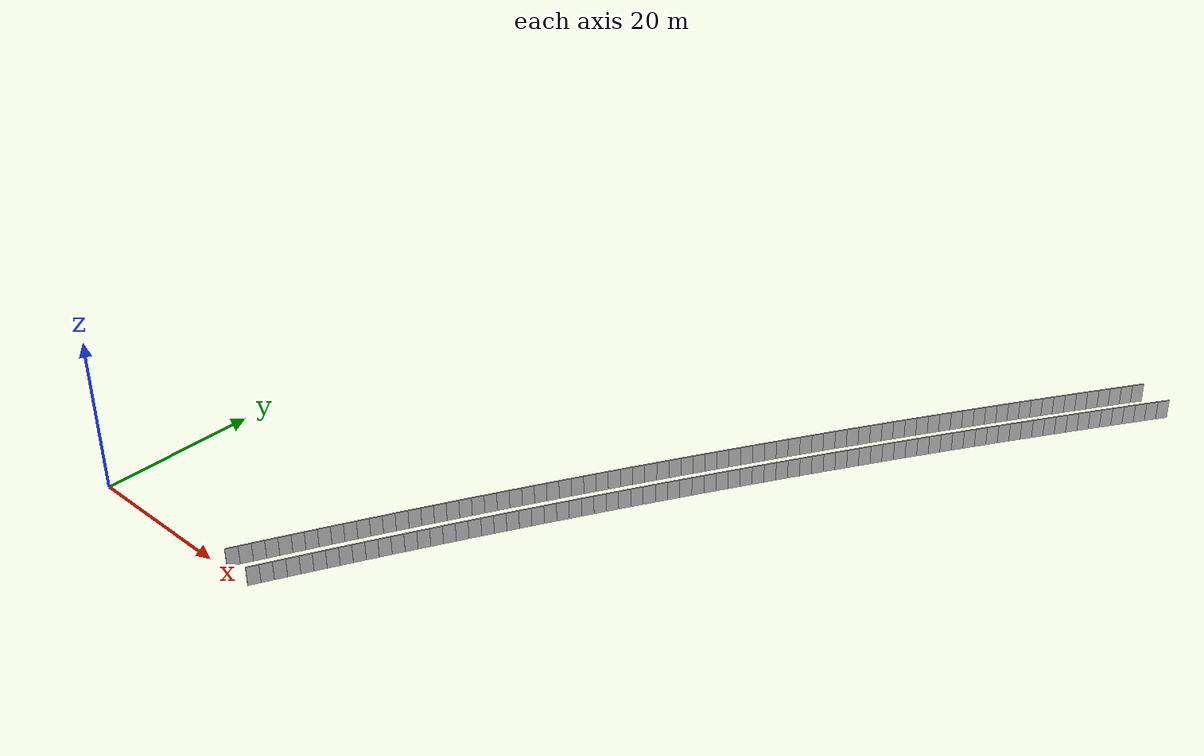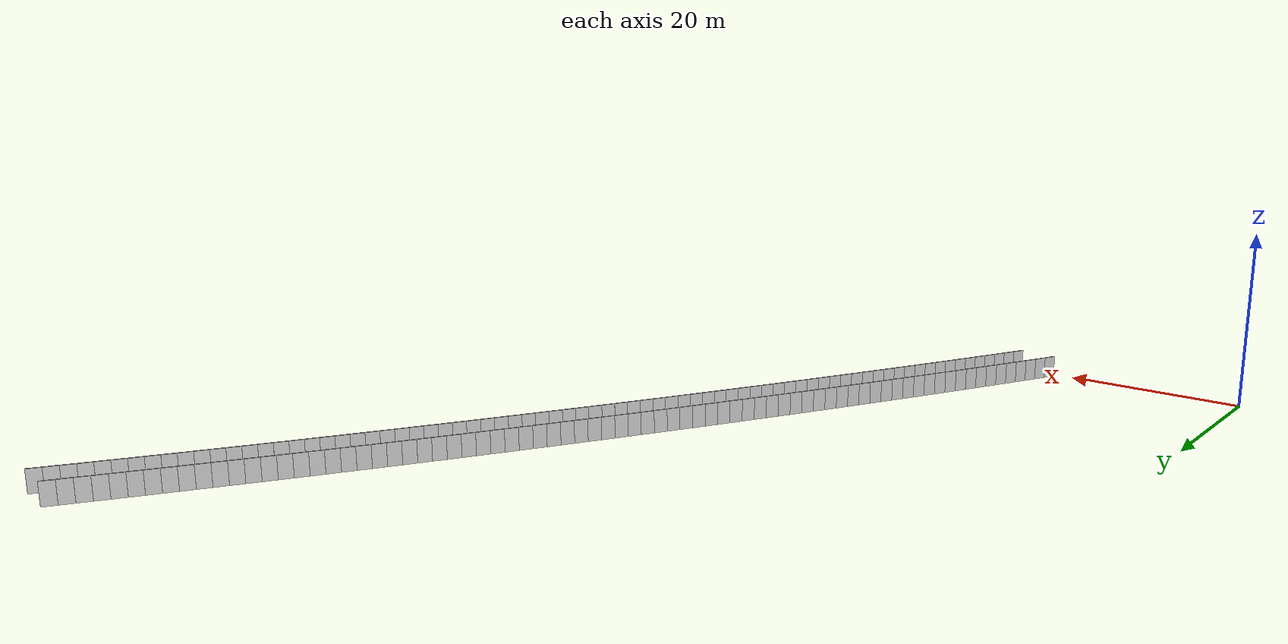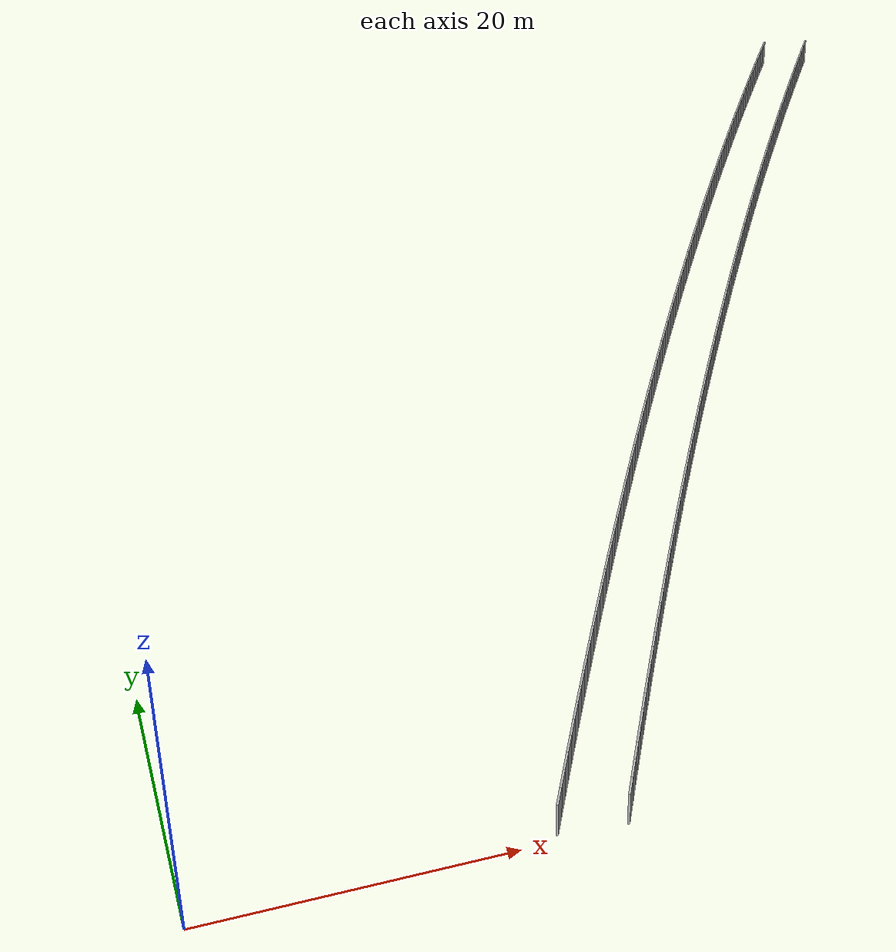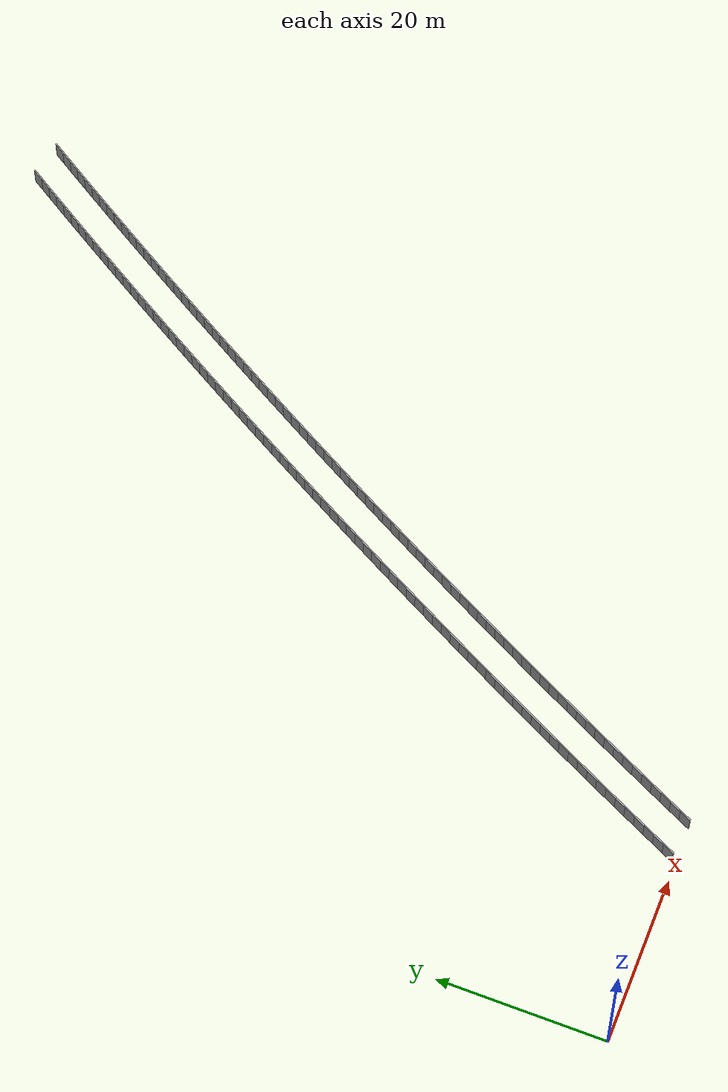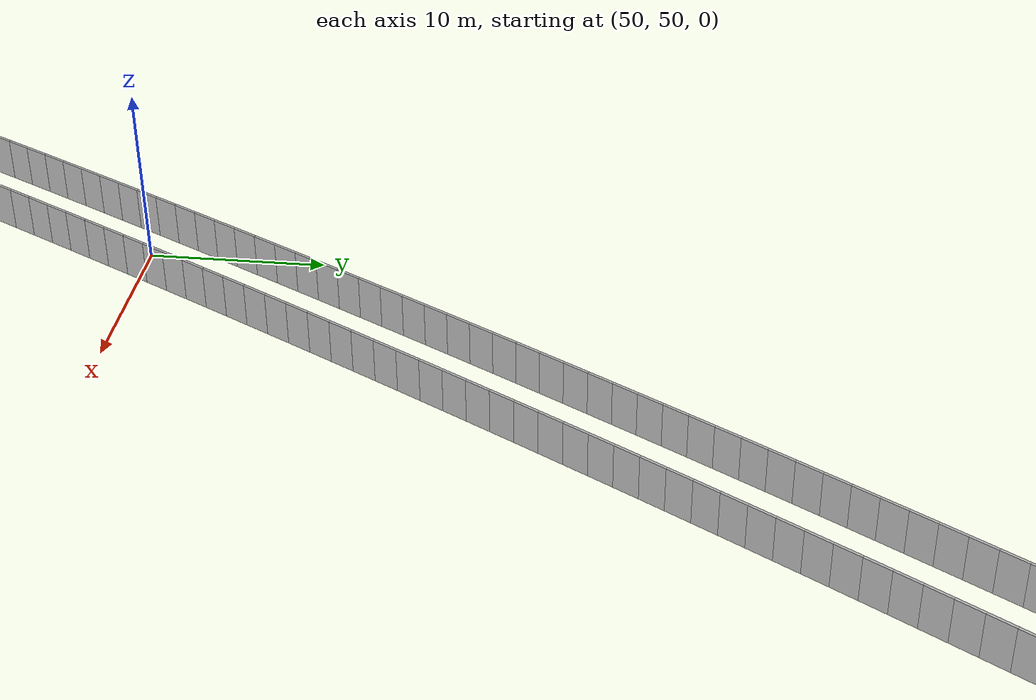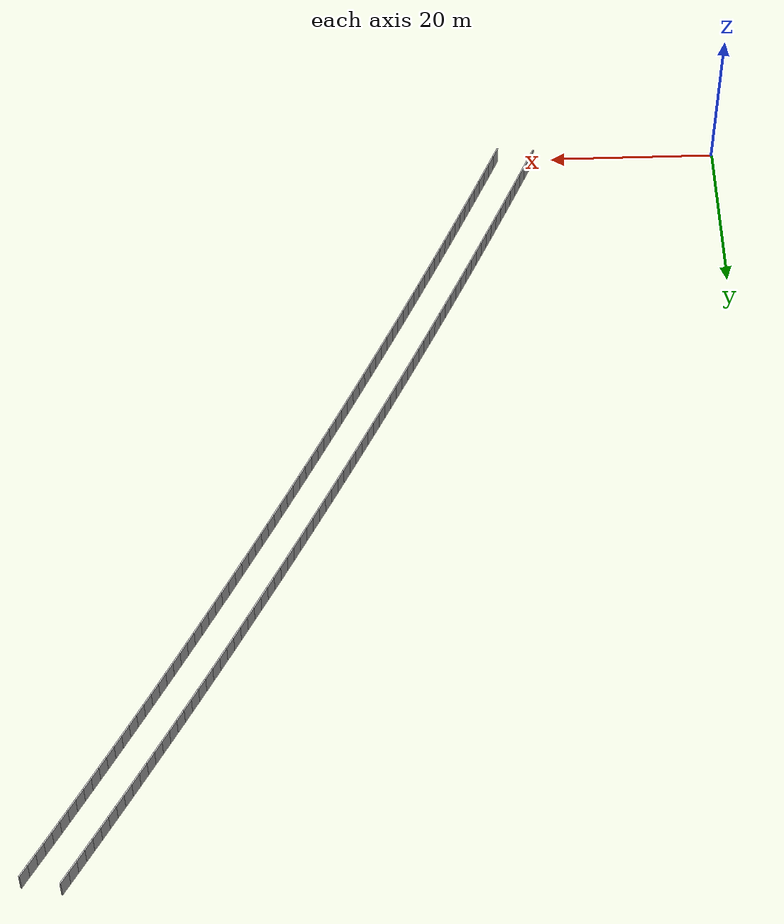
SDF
<?xml version="1.0" ?>
<sdf version="1.6">
  <model name="sps_0217">
    <pose frame="">0 0 0 0 -0 0</pose>
    <static>1</static>
    <self_collide>0</self_collide>
    <allow_auto_disable>0</allow_auto_disable>
    <link name="Wall4891">
      <kinematic>0</kinematic>
      <gravity>1</gravity>
      <self_collide>0</self_collide>
      <collision name="collision">
        <geometry>
          <box>
            <size>1.49664 0.15 2.5</size>
          </box>
        </geometry>
        <pose frame="">0 0 0 0 -0 0</pose>
      </collision>
      <visual name="visual">
        <geometry>
          <box>
            <size>1.49664 0.15 2.5</size>
          </box>
        </geometry>
        <pose frame="">0 0 0 0 -0 0</pose>
        <cast_shadows>1</cast_shadows>
        <transparency>0.0</transparency>
      </visual>
      <pose frame="">81.4339 98.8159 1.25 0 0 -2.13633</pose>
    </link>
    <link name="Wall4892">
      <kinematic>0</kinematic>
      <gravity>1</gravity>
      <self_collide>0</self_collide>
      <collision name="collision">
        <geometry>
          <box>
            <size>1.49649 0.15 2.5</size>
          </box>
        </geometry>
        <pose frame="">0 0 0 0 -0 0</pose>
      </collision>
      <visual name="visual">
        <geometry>
          <box>
            <size>1.49649 0.15 2.5</size>
          </box>
        </geometry>
        <pose frame="">0 0 0 0 -0 0</pose>
        <cast_shadows>1</cast_shadows>
        <transparency>0.0</transparency>
      </visual>
      <pose frame="">80.633 97.5517 1.25 0 0 -2.13466</pose>
    </link>
    <link name="Wall4893">
      <kinematic>0</kinematic>
      <gravity>1</gravity>
      <self_collide>0</self_collide>
      <collision name="collision">
        <geometry>
          <box>
            <size>1.49655 0.15 2.5</size>
          </box>
        </geometry>
        <pose frame="">0 0 0 0 -0 0</pose>
      </collision>
      <visual name="visual">
        <geometry>
          <box>
            <size>1.49655 0.15 2.5</size>
          </box>
        </geometry>
        <pose frame="">0 0 0 0 -0 0</pose>
        <cast_shadows>1</cast_shadows>
        <transparency>0.0</transparency>
      </visual>
      <pose frame="">79.8342 96.2862 1.25 0 0 -2.13304</pose>
    </link>
    <link name="Wall4894">
      <kinematic>0</kinematic>
      <gravity>1</gravity>
      <self_collide>0</self_collide>
      <collision name="collision">
        <geometry>
          <box>
            <size>1.49655 0.15 2.5</size>
          </box>
        </geometry>
        <pose frame="">0 0 0 0 -0 0</pose>
      </collision>
      <visual name="visual">
        <geometry>
          <box>
            <size>1.49655 0.15 2.5</size>
          </box>
        </geometry>
        <pose frame="">0 0 0 0 -0 0</pose>
        <cast_shadows>1</cast_shadows>
        <transparency>0.0</transparency>
      </visual>
      <pose frame="">79.0373 95.0194 1.25 0 0 -2.1315</pose>
    </link>
    <link name="Wall4895">
      <kinematic>0</kinematic>
      <gravity>1</gravity>
      <self_collide>0</self_collide>
      <collision name="collision">
        <geometry>
          <box>
            <size>1.49648 0.15 2.5</size>
          </box>
        </geometry>
        <pose frame="">0 0 0 0 -0 0</pose>
      </collision>
      <visual name="visual">
        <geometry>
          <box>
            <size>1.49648 0.15 2.5</size>
          </box>
        </geometry>
        <pose frame="">0 0 0 0 -0 0</pose>
        <cast_shadows>1</cast_shadows>
        <transparency>0.0</transparency>
      </visual>
      <pose frame="">78.2425 93.7514 1.25 0 0 -2.12989</pose>
    </link>
    <link name="Wall4896">
      <kinematic>0</kinematic>
      <gravity>1</gravity>
      <self_collide>0</self_collide>
      <collision name="collision">
        <geometry>
          <box>
            <size>1.49633 0.15 2.5</size>
          </box>
        </geometry>
        <pose frame="">0 0 0 0 -0 0</pose>
      </collision>
      <visual name="visual">
        <geometry>
          <box>
            <size>1.49633 0.15 2.5</size>
          </box>
        </geometry>
        <pose frame="">0 0 0 0 -0 0</pose>
        <cast_shadows>1</cast_shadows>
        <transparency>0.0</transparency>
      </visual>
      <pose frame="">77.4499 92.4822 1.25 0 0 -2.12827</pose>
    </link>
    <link name="Wall4897">
      <kinematic>0</kinematic>
      <gravity>1</gravity>
      <self_collide>0</self_collide>
      <collision name="collision">
        <geometry>
          <box>
            <size>1.49661 0.15 2.5</size>
          </box>
        </geometry>
        <pose frame="">0 0 0 0 -0 0</pose>
      </collision>
      <visual name="visual">
        <geometry>
          <box>
            <size>1.49661 0.15 2.5</size>
          </box>
        </geometry>
        <pose frame="">0 0 0 0 -0 0</pose>
        <cast_shadows>1</cast_shadows>
        <transparency>0.0</transparency>
      </visual>
      <pose frame="">76.6591 91.2117 1.25 0 0 -2.12672</pose>
    </link>
    <link name="Wall4898">
      <kinematic>0</kinematic>
      <gravity>1</gravity>
      <self_collide>0</self_collide>
      <collision name="collision">
        <geometry>
          <box>
            <size>1.49663 0.15 2.5</size>
          </box>
        </geometry>
        <pose frame="">0 0 0 0 -0 0</pose>
      </collision>
      <visual name="visual">
        <geometry>
          <box>
            <size>1.49663 0.15 2.5</size>
          </box>
        </geometry>
        <pose frame="">0 0 0 0 -0 0</pose>
        <cast_shadows>1</cast_shadows>
        <transparency>0.0</transparency>
      </visual>
      <pose frame="">75.8703 89.9399 1.25 0 0 -2.12527</pose>
    </link>
    <link name="Wall4899">
      <kinematic>0</kinematic>
      <gravity>1</gravity>
      <self_collide>0</self_collide>
      <collision name="collision">
        <geometry>
          <box>
            <size>1.49649 0.15 2.5</size>
          </box>
        </geometry>
        <pose frame="">0 0 0 0 -0 0</pose>
      </collision>
      <visual name="visual">
        <geometry>
          <box>
            <size>1.49649 0.15 2.5</size>
          </box>
        </geometry>
        <pose frame="">0 0 0 0 -0 0</pose>
        <cast_shadows>1</cast_shadows>
        <transparency>0.0</transparency>
      </visual>
      <pose frame="">75.0834 88.6669 1.25 0 0 -2.12365</pose>
    </link>
    <link name="Wall4900">
      <kinematic>0</kinematic>
      <gravity>1</gravity>
      <self_collide>0</self_collide>
      <collision name="collision">
        <geometry>
          <box>
            <size>1.49668 0.15 2.5</size>
          </box>
        </geometry>
        <pose frame="">0 0 0 0 -0 0</pose>
      </collision>
      <visual name="visual">
        <geometry>
          <box>
            <size>1.49668 0.15 2.5</size>
          </box>
        </geometry>
        <pose frame="">0 0 0 0 -0 0</pose>
        <cast_shadows>1</cast_shadows>
        <transparency>0.0</transparency>
      </visual>
      <pose frame="">74.2985 87.3926 1.25 0 0 -2.12199</pose>
    </link>
    <link name="Wall4901">
      <kinematic>0</kinematic>
      <gravity>1</gravity>
      <self_collide>0</self_collide>
      <collision name="collision">
        <geometry>
          <box>
            <size>1.49649 0.15 2.5</size>
          </box>
        </geometry>
        <pose frame="">0 0 0 0 -0 0</pose>
      </collision>
      <visual name="visual">
        <geometry>
          <box>
            <size>1.49649 0.15 2.5</size>
          </box>
        </geometry>
        <pose frame="">0 0 0 0 -0 0</pose>
        <cast_shadows>1</cast_shadows>
        <transparency>0.0</transparency>
      </visual>
      <pose frame="">73.5159 86.117 1.25 0 0 -2.1203</pose>
    </link>
    <link name="Wall4902">
      <kinematic>0</kinematic>
      <gravity>1</gravity>
      <self_collide>0</self_collide>
      <collision name="collision">
        <geometry>
          <box>
            <size>1.49635 0.15 2.5</size>
          </box>
        </geometry>
        <pose frame="">0 0 0 0 -0 0</pose>
      </collision>
      <visual name="visual">
        <geometry>
          <box>
            <size>1.49635 0.15 2.5</size>
          </box>
        </geometry>
        <pose frame="">0 0 0 0 -0 0</pose>
        <cast_shadows>1</cast_shadows>
        <transparency>0.0</transparency>
      </visual>
      <pose frame="">72.7353 84.8403 1.25 0 0 -2.11882</pose>
    </link>
    <link name="Wall4903">
      <kinematic>0</kinematic>
      <gravity>1</gravity>
      <self_collide>0</self_collide>
      <collision name="collision">
        <geometry>
          <box>
            <size>1.49669 0.15 2.5</size>
          </box>
        </geometry>
        <pose frame="">0 0 0 0 -0 0</pose>
      </collision>
      <visual name="visual">
        <geometry>
          <box>
            <size>1.49669 0.15 2.5</size>
          </box>
        </geometry>
        <pose frame="">0 0 0 0 -0 0</pose>
        <cast_shadows>1</cast_shadows>
        <transparency>0.0</transparency>
      </visual>
      <pose frame="">71.9567 83.5623 1.25 0 0 -2.11715</pose>
    </link>
    <link name="Wall4904">
      <kinematic>0</kinematic>
      <gravity>1</gravity>
      <self_collide>0</self_collide>
      <collision name="collision">
        <geometry>
          <box>
            <size>1.49645 0.15 2.5</size>
          </box>
        </geometry>
        <pose frame="">0 0 0 0 -0 0</pose>
      </collision>
      <visual name="visual">
        <geometry>
          <box>
            <size>1.49645 0.15 2.5</size>
          </box>
        </geometry>
        <pose frame="">0 0 0 0 -0 0</pose>
        <cast_shadows>1</cast_shadows>
        <transparency>0.0</transparency>
      </visual>
      <pose frame="">71.18 82.283 1.25 0 0 -2.11563</pose>
    </link>
    <link name="Wall4905">
      <kinematic>0</kinematic>
      <gravity>1</gravity>
      <self_collide>0</self_collide>
      <collision name="collision">
        <geometry>
          <box>
            <size>1.49648 0.15 2.5</size>
          </box>
        </geometry>
        <pose frame="">0 0 0 0 -0 0</pose>
      </collision>
      <visual name="visual">
        <geometry>
          <box>
            <size>1.49648 0.15 2.5</size>
          </box>
        </geometry>
        <pose frame="">0 0 0 0 -0 0</pose>
        <cast_shadows>1</cast_shadows>
        <transparency>0.0</transparency>
      </visual>
      <pose frame="">70.4054 81.0026 1.25 0 0 -2.11409</pose>
    </link>
    <link name="Wall4906">
      <kinematic>0</kinematic>
      <gravity>1</gravity>
      <self_collide>0</self_collide>
      <collision name="collision">
        <geometry>
          <box>
            <size>1.49665 0.15 2.5</size>
          </box>
        </geometry>
        <pose frame="">0 0 0 0 -0 0</pose>
      </collision>
      <visual name="visual">
        <geometry>
          <box>
            <size>1.49665 0.15 2.5</size>
          </box>
        </geometry>
        <pose frame="">0 0 0 0 -0 0</pose>
        <cast_shadows>1</cast_shadows>
        <transparency>0.0</transparency>
      </visual>
      <pose frame="">69.6328 79.7209 1.25 0 0 -2.11245</pose>
    </link>
    <link name="Wall4907">
      <kinematic>0</kinematic>
      <gravity>1</gravity>
      <self_collide>0</self_collide>
      <collision name="collision">
        <geometry>
          <box>
            <size>1.49645 0.15 2.5</size>
          </box>
        </geometry>
        <pose frame="">0 0 0 0 -0 0</pose>
      </collision>
      <visual name="visual">
        <geometry>
          <box>
            <size>1.49645 0.15 2.5</size>
          </box>
        </geometry>
        <pose frame="">0 0 0 0 -0 0</pose>
        <cast_shadows>1</cast_shadows>
        <transparency>0.0</transparency>
      </visual>
      <pose frame="">68.8622 78.438 1.25 0 0 -2.11096</pose>
    </link>
    <link name="Wall4908">
      <kinematic>0</kinematic>
      <gravity>1</gravity>
      <self_collide>0</self_collide>
      <collision name="collision">
        <geometry>
          <box>
            <size>1.49652 0.15 2.5</size>
          </box>
        </geometry>
        <pose frame="">0 0 0 0 -0 0</pose>
      </collision>
      <visual name="visual">
        <geometry>
          <box>
            <size>1.49652 0.15 2.5</size>
          </box>
        </geometry>
        <pose frame="">0 0 0 0 -0 0</pose>
        <cast_shadows>1</cast_shadows>
        <transparency>0.0</transparency>
      </visual>
      <pose frame="">68.0937 77.1539 1.25 0 0 -2.10922</pose>
    </link>
    <link name="Wall4909">
      <kinematic>0</kinematic>
      <gravity>1</gravity>
      <self_collide>0</self_collide>
      <collision name="collision">
        <geometry>
          <box>
            <size>1.49633 0.15 2.5</size>
          </box>
        </geometry>
        <pose frame="">0 0 0 0 -0 0</pose>
      </collision>
      <visual name="visual">
        <geometry>
          <box>
            <size>1.49633 0.15 2.5</size>
          </box>
        </geometry>
        <pose frame="">0 0 0 0 -0 0</pose>
        <cast_shadows>1</cast_shadows>
        <transparency>0.0</transparency>
      </visual>
      <pose frame="">67.3274 75.8686 1.25 0 0 -2.10773</pose>
    </link>
    <link name="Wall4910">
      <kinematic>0</kinematic>
      <gravity>1</gravity>
      <self_collide>0</self_collide>
      <collision name="collision">
        <geometry>
          <box>
            <size>1.49669 0.15 2.5</size>
          </box>
        </geometry>
        <pose frame="">0 0 0 0 -0 0</pose>
      </collision>
      <visual name="visual">
        <geometry>
          <box>
            <size>1.49669 0.15 2.5</size>
          </box>
        </geometry>
        <pose frame="">0 0 0 0 -0 0</pose>
        <cast_shadows>1</cast_shadows>
        <transparency>0.0</transparency>
      </visual>
      <pose frame="">66.5629 74.5821 1.25 0 0 -2.10622</pose>
    </link>
    <link name="Wall4911">
      <kinematic>0</kinematic>
      <gravity>1</gravity>
      <self_collide>0</self_collide>
      <collision name="collision">
        <geometry>
          <box>
            <size>1.49656 0.15 2.5</size>
          </box>
        </geometry>
        <pose frame="">0 0 0 0 -0 0</pose>
      </collision>
      <visual name="visual">
        <geometry>
          <box>
            <size>1.49656 0.15 2.5</size>
          </box>
        </geometry>
        <pose frame="">0 0 0 0 -0 0</pose>
        <cast_shadows>1</cast_shadows>
        <transparency>0.0</transparency>
      </visual>
      <pose frame="">65.8003 73.2943 1.25 0 0 -2.10456</pose>
    </link>
    <link name="Wall4912">
      <kinematic>0</kinematic>
      <gravity>1</gravity>
      <self_collide>0</self_collide>
      <collision name="collision">
        <geometry>
          <box>
            <size>1.49643 0.15 2.5</size>
          </box>
        </geometry>
        <pose frame="">0 0 0 0 -0 0</pose>
      </collision>
      <visual name="visual">
        <geometry>
          <box>
            <size>1.49643 0.15 2.5</size>
          </box>
        </geometry>
        <pose frame="">0 0 0 0 -0 0</pose>
        <cast_shadows>1</cast_shadows>
        <transparency>0.0</transparency>
      </visual>
      <pose frame="">65.0399 72.0054 1.25 0 0 -2.10305</pose>
    </link>
    <link name="Wall4913">
      <kinematic>0</kinematic>
      <gravity>1</gravity>
      <self_collide>0</self_collide>
      <collision name="collision">
        <geometry>
          <box>
            <size>1.49648 0.15 2.5</size>
          </box>
        </geometry>
        <pose frame="">0 0 0 0 -0 0</pose>
      </collision>
      <visual name="visual">
        <geometry>
          <box>
            <size>1.49648 0.15 2.5</size>
          </box>
        </geometry>
        <pose frame="">0 0 0 0 -0 0</pose>
        <cast_shadows>1</cast_shadows>
        <transparency>0.0</transparency>
      </visual>
      <pose frame="">64.2816 70.7153 1.25 0 0 -2.10133</pose>
    </link>
    <link name="Wall4914">
      <kinematic>0</kinematic>
      <gravity>1</gravity>
      <self_collide>0</self_collide>
      <collision name="collision">
        <geometry>
          <box>
            <size>1.49661 0.15 2.5</size>
          </box>
        </geometry>
        <pose frame="">0 0 0 0 -0 0</pose>
      </collision>
      <visual name="visual">
        <geometry>
          <box>
            <size>1.49661 0.15 2.5</size>
          </box>
        </geometry>
        <pose frame="">0 0 0 0 -0 0</pose>
        <cast_shadows>1</cast_shadows>
        <transparency>0.0</transparency>
      </visual>
      <pose frame="">63.5254 69.4239 1.25 0 0 -2.09986</pose>
    </link>
    <link name="Wall4915">
      <kinematic>0</kinematic>
      <gravity>1</gravity>
      <self_collide>0</self_collide>
      <collision name="collision">
        <geometry>
          <box>
            <size>1.49658 0.15 2.5</size>
          </box>
        </geometry>
        <pose frame="">0 0 0 0 -0 0</pose>
      </collision>
      <visual name="visual">
        <geometry>
          <box>
            <size>1.49658 0.15 2.5</size>
          </box>
        </geometry>
        <pose frame="">0 0 0 0 -0 0</pose>
        <cast_shadows>1</cast_shadows>
        <transparency>0.0</transparency>
      </visual>
      <pose frame="">62.771 68.1313 1.25 0 0 -2.09821</pose>
    </link>
    <link name="Wall4916">
      <kinematic>0</kinematic>
      <gravity>1</gravity>
      <self_collide>0</self_collide>
      <collision name="collision">
        <geometry>
          <box>
            <size>1.49654 0.15 2.5</size>
          </box>
        </geometry>
        <pose frame="">0 0 0 0 -0 0</pose>
      </collision>
      <visual name="visual">
        <geometry>
          <box>
            <size>1.49654 0.15 2.5</size>
          </box>
        </geometry>
        <pose frame="">0 0 0 0 -0 0</pose>
        <cast_shadows>1</cast_shadows>
        <transparency>0.0</transparency>
      </visual>
      <pose frame="">62.0189 66.8375 1.25 0 0 -2.09662</pose>
    </link>
    <link name="Wall4917">
      <kinematic>0</kinematic>
      <gravity>1</gravity>
      <self_collide>0</self_collide>
      <collision name="collision">
        <geometry>
          <box>
            <size>1.49637 0.15 2.5</size>
          </box>
        </geometry>
        <pose frame="">0 0 0 0 -0 0</pose>
      </collision>
      <visual name="visual">
        <geometry>
          <box>
            <size>1.49637 0.15 2.5</size>
          </box>
        </geometry>
        <pose frame="">0 0 0 0 -0 0</pose>
        <cast_shadows>1</cast_shadows>
        <transparency>0.0</transparency>
      </visual>
      <pose frame="">61.2688 65.5426 1.25 0 0 -2.09504</pose>
    </link>
    <link name="Wall4918">
      <kinematic>0</kinematic>
      <gravity>1</gravity>
      <self_collide>0</self_collide>
      <collision name="collision">
        <geometry>
          <box>
            <size>1.49667 0.15 2.5</size>
          </box>
        </geometry>
        <pose frame="">0 0 0 0 -0 0</pose>
      </collision>
      <visual name="visual">
        <geometry>
          <box>
            <size>1.49667 0.15 2.5</size>
          </box>
        </geometry>
        <pose frame="">0 0 0 0 -0 0</pose>
        <cast_shadows>1</cast_shadows>
        <transparency>0.0</transparency>
      </visual>
      <pose frame="">60.5207 64.2465 1.25 0 0 -2.09351</pose>
    </link>
    <link name="Wall4919">
      <kinematic>0</kinematic>
      <gravity>1</gravity>
      <self_collide>0</self_collide>
      <collision name="collision">
        <geometry>
          <box>
            <size>1.49633 0.15 2.5</size>
          </box>
        </geometry>
        <pose frame="">0 0 0 0 -0 0</pose>
      </collision>
      <visual name="visual">
        <geometry>
          <box>
            <size>1.49633 0.15 2.5</size>
          </box>
        </geometry>
        <pose frame="">0 0 0 0 -0 0</pose>
        <cast_shadows>1</cast_shadows>
        <transparency>0.0</transparency>
      </visual>
      <pose frame="">59.7746 62.9492 1.25 0 0 -2.09181</pose>
    </link>
    <link name="Wall4920">
      <kinematic>0</kinematic>
      <gravity>1</gravity>
      <self_collide>0</self_collide>
      <collision name="collision">
        <geometry>
          <box>
            <size>1.49664 0.15 2.5</size>
          </box>
        </geometry>
        <pose frame="">0 0 0 0 -0 0</pose>
      </collision>
      <visual name="visual">
        <geometry>
          <box>
            <size>1.49664 0.15 2.5</size>
          </box>
        </geometry>
        <pose frame="">0 0 0 0 -0 0</pose>
        <cast_shadows>1</cast_shadows>
        <transparency>0.0</transparency>
      </visual>
      <pose frame="">59.0308 61.6507 1.25 0 0 -2.09028</pose>
    </link>
    <link name="Wall4921">
      <kinematic>0</kinematic>
      <gravity>1</gravity>
      <self_collide>0</self_collide>
      <collision name="collision">
        <geometry>
          <box>
            <size>1.49645 0.15 2.5</size>
          </box>
        </geometry>
        <pose frame="">0 0 0 0 -0 0</pose>
      </collision>
      <visual name="visual">
        <geometry>
          <box>
            <size>1.49645 0.15 2.5</size>
          </box>
        </geometry>
        <pose frame="">0 0 0 0 -0 0</pose>
        <cast_shadows>1</cast_shadows>
        <transparency>0.0</transparency>
      </visual>
      <pose frame="">58.2889 60.351 1.25 0 0 -2.08866</pose>
    </link>
    <link name="Wall4922">
      <kinematic>0</kinematic>
      <gravity>1</gravity>
      <self_collide>0</self_collide>
      <collision name="collision">
        <geometry>
          <box>
            <size>1.49649 0.15 2.5</size>
          </box>
        </geometry>
        <pose frame="">0 0 0 0 -0 0</pose>
      </collision>
      <visual name="visual">
        <geometry>
          <box>
            <size>1.49649 0.15 2.5</size>
          </box>
        </geometry>
        <pose frame="">0 0 0 0 -0 0</pose>
        <cast_shadows>1</cast_shadows>
        <transparency>0.0</transparency>
      </visual>
      <pose frame="">57.5491 59.0502 1.25 0 0 -2.08714</pose>
    </link>
    <link name="Wall4923">
      <kinematic>0</kinematic>
      <gravity>1</gravity>
      <self_collide>0</self_collide>
      <collision name="collision">
        <geometry>
          <box>
            <size>1.49656 0.15 2.5</size>
          </box>
        </geometry>
        <pose frame="">0 0 0 0 -0 0</pose>
      </collision>
      <visual name="visual">
        <geometry>
          <box>
            <size>1.49656 0.15 2.5</size>
          </box>
        </geometry>
        <pose frame="">0 0 0 0 -0 0</pose>
        <cast_shadows>1</cast_shadows>
        <transparency>0.0</transparency>
      </visual>
      <pose frame="">56.8112 57.7482 1.25 0 0 -2.08557</pose>
    </link>
    <link name="Wall4924">
      <kinematic>0</kinematic>
      <gravity>1</gravity>
      <self_collide>0</self_collide>
      <collision name="collision">
        <geometry>
          <box>
            <size>1.49658 0.15 2.5</size>
          </box>
        </geometry>
        <pose frame="">0 0 0 0 -0 0</pose>
      </collision>
      <visual name="visual">
        <geometry>
          <box>
            <size>1.49658 0.15 2.5</size>
          </box>
        </geometry>
        <pose frame="">0 0 0 0 -0 0</pose>
        <cast_shadows>1</cast_shadows>
        <transparency>0.0</transparency>
      </visual>
      <pose frame="">56.0754 56.445 1.25 0 0 -2.08402</pose>
    </link>
    <link name="Wall4925">
      <kinematic>0</kinematic>
      <gravity>1</gravity>
      <self_collide>0</self_collide>
      <collision name="collision">
        <geometry>
          <box>
            <size>1.49654 0.15 2.5</size>
          </box>
        </geometry>
        <pose frame="">0 0 0 0 -0 0</pose>
      </collision>
      <visual name="visual">
        <geometry>
          <box>
            <size>1.49654 0.15 2.5</size>
          </box>
        </geometry>
        <pose frame="">0 0 0 0 -0 0</pose>
        <cast_shadows>1</cast_shadows>
        <transparency>0.0</transparency>
      </visual>
      <pose frame="">55.3418 55.1406 1.25 0 0 -2.0823</pose>
    </link>
    <link name="Wall4926">
      <kinematic>0</kinematic>
      <gravity>1</gravity>
      <self_collide>0</self_collide>
      <collision name="collision">
        <geometry>
          <box>
            <size>1.49652 0.15 2.5</size>
          </box>
        </geometry>
        <pose frame="">0 0 0 0 -0 0</pose>
      </collision>
      <visual name="visual">
        <geometry>
          <box>
            <size>1.49652 0.15 2.5</size>
          </box>
        </geometry>
        <pose frame="">0 0 0 0 -0 0</pose>
        <cast_shadows>1</cast_shadows>
        <transparency>0.0</transparency>
      </visual>
      <pose frame="">54.6102 53.8351 1.25 0 0 -2.08086</pose>
    </link>
    <link name="Wall4927">
      <kinematic>0</kinematic>
      <gravity>1</gravity>
      <self_collide>0</self_collide>
      <collision name="collision">
        <geometry>
          <box>
            <size>1.49652 0.15 2.5</size>
          </box>
        </geometry>
        <pose frame="">0 0 0 0 -0 0</pose>
      </collision>
      <visual name="visual">
        <geometry>
          <box>
            <size>1.49652 0.15 2.5</size>
          </box>
        </geometry>
        <pose frame="">0 0 0 0 -0 0</pose>
        <cast_shadows>1</cast_shadows>
        <transparency>0.0</transparency>
      </visual>
      <pose frame="">53.8805 52.5285 1.25 0 0 -2.07927</pose>
    </link>
    <link name="Wall4928">
      <kinematic>0</kinematic>
      <gravity>1</gravity>
      <self_collide>0</self_collide>
      <collision name="collision">
        <geometry>
          <box>
            <size>1.49652 0.15 2.5</size>
          </box>
        </geometry>
        <pose frame="">0 0 0 0 -0 0</pose>
      </collision>
      <visual name="visual">
        <geometry>
          <box>
            <size>1.49652 0.15 2.5</size>
          </box>
        </geometry>
        <pose frame="">0 0 0 0 -0 0</pose>
        <cast_shadows>1</cast_shadows>
        <transparency>0.0</transparency>
      </visual>
      <pose frame="">53.1531 51.2207 1.25 0 0 -2.07759</pose>
    </link>
    <link name="Wall4929">
      <kinematic>0</kinematic>
      <gravity>1</gravity>
      <self_collide>0</self_collide>
      <collision name="collision">
        <geometry>
          <box>
            <size>1.49626 0.15 2.5</size>
          </box>
        </geometry>
        <pose frame="">0 0 0 0 -0 0</pose>
      </collision>
      <visual name="visual">
        <geometry>
          <box>
            <size>1.49626 0.15 2.5</size>
          </box>
        </geometry>
        <pose frame="">0 0 0 0 -0 0</pose>
        <cast_shadows>1</cast_shadows>
        <transparency>0.0</transparency>
      </visual>
      <pose frame="">52.4277 49.9119 1.25 0 0 -2.0762</pose>
    </link>
    <link name="Wall4930">
      <kinematic>0</kinematic>
      <gravity>1</gravity>
      <self_collide>0</self_collide>
      <collision name="collision">
        <geometry>
          <box>
            <size>1.49672 0.15 2.5</size>
          </box>
        </geometry>
        <pose frame="">0 0 0 0 -0 0</pose>
      </collision>
      <visual name="visual">
        <geometry>
          <box>
            <size>1.49672 0.15 2.5</size>
          </box>
        </geometry>
        <pose frame="">0 0 0 0 -0 0</pose>
        <cast_shadows>1</cast_shadows>
        <transparency>0.0</transparency>
      </visual>
      <pose frame="">51.7044 48.6018 1.25 0 0 -2.0743</pose>
    </link>
    <link name="Wall4931">
      <kinematic>0</kinematic>
      <gravity>1</gravity>
      <self_collide>0</self_collide>
      <collision name="collision">
        <geometry>
          <box>
            <size>1.49653 0.15 2.5</size>
          </box>
        </geometry>
        <pose frame="">0 0 0 0 -0 0</pose>
      </collision>
      <visual name="visual">
        <geometry>
          <box>
            <size>1.49653 0.15 2.5</size>
          </box>
        </geometry>
        <pose frame="">0 0 0 0 -0 0</pose>
        <cast_shadows>1</cast_shadows>
        <transparency>0.0</transparency>
      </visual>
      <pose frame="">50.9832 47.2904 1.25 0 0 -2.07288</pose>
    </link>
    <link name="Wall4932">
      <kinematic>0</kinematic>
      <gravity>1</gravity>
      <self_collide>0</self_collide>
      <collision name="collision">
        <geometry>
          <box>
            <size>1.49649 0.15 2.5</size>
          </box>
        </geometry>
        <pose frame="">0 0 0 0 -0 0</pose>
      </collision>
      <visual name="visual">
        <geometry>
          <box>
            <size>1.49649 0.15 2.5</size>
          </box>
        </geometry>
        <pose frame="">0 0 0 0 -0 0</pose>
        <cast_shadows>1</cast_shadows>
        <transparency>0.0</transparency>
      </visual>
      <pose frame="">50.2641 45.978 1.25 0 0 -2.07122</pose>
    </link>
    <link name="Wall4933">
      <kinematic>0</kinematic>
      <gravity>1</gravity>
      <self_collide>0</self_collide>
      <collision name="collision">
        <geometry>
          <box>
            <size>1.49651 0.15 2.5</size>
          </box>
        </geometry>
        <pose frame="">0 0 0 0 -0 0</pose>
      </collision>
      <visual name="visual">
        <geometry>
          <box>
            <size>1.49651 0.15 2.5</size>
          </box>
        </geometry>
        <pose frame="">0 0 0 0 -0 0</pose>
        <cast_shadows>1</cast_shadows>
        <transparency>0.0</transparency>
      </visual>
      <pose frame="">49.5471 44.6644 1.25 0 0 -2.06954</pose>
    </link>
    <link name="Wall4934">
      <kinematic>0</kinematic>
      <gravity>1</gravity>
      <self_collide>0</self_collide>
      <collision name="collision">
        <geometry>
          <box>
            <size>1.49649 0.15 2.5</size>
          </box>
        </geometry>
        <pose frame="">0 0 0 0 -0 0</pose>
      </collision>
      <visual name="visual">
        <geometry>
          <box>
            <size>1.49649 0.15 2.5</size>
          </box>
        </geometry>
        <pose frame="">0 0 0 0 -0 0</pose>
        <cast_shadows>1</cast_shadows>
        <transparency>0.0</transparency>
      </visual>
      <pose frame="">48.8322 43.3497 1.25 0 0 -2.06816</pose>
    </link>
    <link name="Wall4935">
      <kinematic>0</kinematic>
      <gravity>1</gravity>
      <self_collide>0</self_collide>
      <collision name="collision">
        <geometry>
          <box>
            <size>1.49645 0.15 2.5</size>
          </box>
        </geometry>
        <pose frame="">0 0 0 0 -0 0</pose>
      </collision>
      <visual name="visual">
        <geometry>
          <box>
            <size>1.49645 0.15 2.5</size>
          </box>
        </geometry>
        <pose frame="">0 0 0 0 -0 0</pose>
        <cast_shadows>1</cast_shadows>
        <transparency>0.0</transparency>
      </visual>
      <pose frame="">48.1193 42.034 1.25 0 0 -2.06664</pose>
    </link>
    <link name="Wall4936">
      <kinematic>0</kinematic>
      <gravity>1</gravity>
      <self_collide>0</self_collide>
      <collision name="collision">
        <geometry>
          <box>
            <size>1.49661 0.15 2.5</size>
          </box>
        </geometry>
        <pose frame="">0 0 0 0 -0 0</pose>
      </collision>
      <visual name="visual">
        <geometry>
          <box>
            <size>1.49661 0.15 2.5</size>
          </box>
        </geometry>
        <pose frame="">0 0 0 0 -0 0</pose>
        <cast_shadows>1</cast_shadows>
        <transparency>0.0</transparency>
      </visual>
      <pose frame="">47.4083 40.7171 1.25 0 0 -2.06496</pose>
    </link>
    <link name="Wall4937">
      <kinematic>0</kinematic>
      <gravity>1</gravity>
      <self_collide>0</self_collide>
      <collision name="collision">
        <geometry>
          <box>
            <size>1.49646 0.15 2.5</size>
          </box>
        </geometry>
        <pose frame="">0 0 0 0 -0 0</pose>
      </collision>
      <visual name="visual">
        <geometry>
          <box>
            <size>1.49646 0.15 2.5</size>
          </box>
        </geometry>
        <pose frame="">0 0 0 0 -0 0</pose>
        <cast_shadows>1</cast_shadows>
        <transparency>0.0</transparency>
      </visual>
      <pose frame="">46.6996 39.399 1.25 0 0 -2.0633</pose>
    </link>
    <link name="Wall4938">
      <kinematic>0</kinematic>
      <gravity>1</gravity>
      <self_collide>0</self_collide>
      <collision name="collision">
        <geometry>
          <box>
            <size>1.49658 0.15 2.5</size>
          </box>
        </geometry>
        <pose frame="">0 0 0 0 -0 0</pose>
      </collision>
      <visual name="visual">
        <geometry>
          <box>
            <size>1.49658 0.15 2.5</size>
          </box>
        </geometry>
        <pose frame="">0 0 0 0 -0 0</pose>
        <cast_shadows>1</cast_shadows>
        <transparency>0.0</transparency>
      </visual>
      <pose frame="">45.9931 38.0798 1.25 0 0 -2.06173</pose>
    </link>
    <link name="Wall4939">
      <kinematic>0</kinematic>
      <gravity>1</gravity>
      <self_collide>0</self_collide>
      <collision name="collision">
        <geometry>
          <box>
            <size>1.49652 0.15 2.5</size>
          </box>
        </geometry>
        <pose frame="">0 0 0 0 -0 0</pose>
      </collision>
      <visual name="visual">
        <geometry>
          <box>
            <size>1.49652 0.15 2.5</size>
          </box>
        </geometry>
        <pose frame="">0 0 0 0 -0 0</pose>
        <cast_shadows>1</cast_shadows>
        <transparency>0.0</transparency>
      </visual>
      <pose frame="">45.2885 36.7595 1.25 0 0 -2.06027</pose>
    </link>
    <link name="Wall4940">
      <kinematic>0</kinematic>
      <gravity>1</gravity>
      <self_collide>0</self_collide>
      <collision name="collision">
        <geometry>
          <box>
            <size>1.49652 0.15 2.5</size>
          </box>
        </geometry>
        <pose frame="">0 0 0 0 -0 0</pose>
      </collision>
      <visual name="visual">
        <geometry>
          <box>
            <size>1.49652 0.15 2.5</size>
          </box>
        </geometry>
        <pose frame="">0 0 0 0 -0 0</pose>
        <cast_shadows>1</cast_shadows>
        <transparency>0.0</transparency>
      </visual>
      <pose frame="">44.586 35.4381 1.25 0 0 -2.05861</pose>
    </link>
    <link name="Wall4941">
      <kinematic>0</kinematic>
      <gravity>1</gravity>
      <self_collide>0</self_collide>
      <collision name="collision">
        <geometry>
          <box>
            <size>1.49641 0.15 2.5</size>
          </box>
        </geometry>
        <pose frame="">0 0 0 0 -0 0</pose>
      </collision>
      <visual name="visual">
        <geometry>
          <box>
            <size>1.49641 0.15 2.5</size>
          </box>
        </geometry>
        <pose frame="">0 0 0 0 -0 0</pose>
        <cast_shadows>1</cast_shadows>
        <transparency>0.0</transparency>
      </visual>
      <pose frame="">43.8856 34.1156 1.25 0 0 -2.05699</pose>
    </link>
    <link name="Wall4942">
      <kinematic>0</kinematic>
      <gravity>1</gravity>
      <self_collide>0</self_collide>
      <collision name="collision">
        <geometry>
          <box>
            <size>1.49655 0.15 2.5</size>
          </box>
        </geometry>
        <pose frame="">0 0 0 0 -0 0</pose>
      </collision>
      <visual name="visual">
        <geometry>
          <box>
            <size>1.49655 0.15 2.5</size>
          </box>
        </geometry>
        <pose frame="">0 0 0 0 -0 0</pose>
        <cast_shadows>1</cast_shadows>
        <transparency>0.0</transparency>
      </visual>
      <pose frame="">43.1874 32.792 1.25 0 0 -2.05542</pose>
    </link>
    <link name="Wall4943">
      <kinematic>0</kinematic>
      <gravity>1</gravity>
      <self_collide>0</self_collide>
      <collision name="collision">
        <geometry>
          <box>
            <size>1.49647 0.15 2.5</size>
          </box>
        </geometry>
        <pose frame="">0 0 0 0 -0 0</pose>
      </collision>
      <visual name="visual">
        <geometry>
          <box>
            <size>1.49647 0.15 2.5</size>
          </box>
        </geometry>
        <pose frame="">0 0 0 0 -0 0</pose>
        <cast_shadows>1</cast_shadows>
        <transparency>0.0</transparency>
      </visual>
      <pose frame="">42.4912 31.4673 1.25 0 0 -2.05393</pose>
    </link>
    <link name="Wall4944">
      <kinematic>0</kinematic>
      <gravity>1</gravity>
      <self_collide>0</self_collide>
      <collision name="collision">
        <geometry>
          <box>
            <size>1.49654 0.15 2.5</size>
          </box>
        </geometry>
        <pose frame="">0 0 0 0 -0 0</pose>
      </collision>
      <visual name="visual">
        <geometry>
          <box>
            <size>1.49654 0.15 2.5</size>
          </box>
        </geometry>
        <pose frame="">0 0 0 0 -0 0</pose>
        <cast_shadows>1</cast_shadows>
        <transparency>0.0</transparency>
      </visual>
      <pose frame="">41.7971 30.1415 1.25 0 0 -2.05225</pose>
    </link>
    <link name="Wall4945">
      <kinematic>0</kinematic>
      <gravity>1</gravity>
      <self_collide>0</self_collide>
      <collision name="collision">
        <geometry>
          <box>
            <size>1.49655 0.15 2.5</size>
          </box>
        </geometry>
        <pose frame="">0 0 0 0 -0 0</pose>
      </collision>
      <visual name="visual">
        <geometry>
          <box>
            <size>1.49655 0.15 2.5</size>
          </box>
        </geometry>
        <pose frame="">0 0 0 0 -0 0</pose>
        <cast_shadows>1</cast_shadows>
        <transparency>0.0</transparency>
      </visual>
      <pose frame="">41.1052 28.8145 1.25 0 0 -2.05059</pose>
    </link>
    <link name="Wall4946">
      <kinematic>0</kinematic>
      <gravity>1</gravity>
      <self_collide>0</self_collide>
      <collision name="collision">
        <geometry>
          <box>
            <size>1.49662 0.15 2.5</size>
          </box>
        </geometry>
        <pose frame="">0 0 0 0 -0 0</pose>
      </collision>
      <visual name="visual">
        <geometry>
          <box>
            <size>1.49662 0.15 2.5</size>
          </box>
        </geometry>
        <pose frame="">0 0 0 0 -0 0</pose>
        <cast_shadows>1</cast_shadows>
        <transparency>0.0</transparency>
      </visual>
      <pose frame="">40.4154 27.4864 1.25 0 0 -2.04918</pose>
    </link>
    <link name="Wall4947">
      <kinematic>0</kinematic>
      <gravity>1</gravity>
      <self_collide>0</self_collide>
      <collision name="collision">
        <geometry>
          <box>
            <size>1.49651 0.15 2.5</size>
          </box>
        </geometry>
        <pose frame="">0 0 0 0 -0 0</pose>
      </collision>
      <visual name="visual">
        <geometry>
          <box>
            <size>1.49651 0.15 2.5</size>
          </box>
        </geometry>
        <pose frame="">0 0 0 0 -0 0</pose>
        <cast_shadows>1</cast_shadows>
        <transparency>0.0</transparency>
      </visual>
      <pose frame="">39.7275 26.1573 1.25 0 0 -2.04761</pose>
    </link>
    <link name="Wall4948">
      <kinematic>0</kinematic>
      <gravity>1</gravity>
      <self_collide>0</self_collide>
      <collision name="collision">
        <geometry>
          <box>
            <size>1.49656 0.15 2.5</size>
          </box>
        </geometry>
        <pose frame="">0 0 0 0 -0 0</pose>
      </collision>
      <visual name="visual">
        <geometry>
          <box>
            <size>1.49656 0.15 2.5</size>
          </box>
        </geometry>
        <pose frame="">0 0 0 0 -0 0</pose>
        <cast_shadows>1</cast_shadows>
        <transparency>0.0</transparency>
      </visual>
      <pose frame="">39.0418 24.8271 1.25 0 0 -2.0459</pose>
    </link>
    <link name="Wall4949">
      <kinematic>0</kinematic>
      <gravity>1</gravity>
      <self_collide>0</self_collide>
      <collision name="collision">
        <geometry>
          <box>
            <size>1.49645 0.15 2.5</size>
          </box>
        </geometry>
        <pose frame="">0 0 0 0 -0 0</pose>
      </collision>
      <visual name="visual">
        <geometry>
          <box>
            <size>1.49645 0.15 2.5</size>
          </box>
        </geometry>
        <pose frame="">0 0 0 0 -0 0</pose>
        <cast_shadows>1</cast_shadows>
        <transparency>0.0</transparency>
      </visual>
      <pose frame="">38.3583 23.4958 1.25 0 0 -2.04433</pose>
    </link>
    <link name="Wall4950">
      <kinematic>0</kinematic>
      <gravity>1</gravity>
      <self_collide>0</self_collide>
      <collision name="collision">
        <geometry>
          <box>
            <size>1.49646 0.15 2.5</size>
          </box>
        </geometry>
        <pose frame="">0 0 0 0 -0 0</pose>
      </collision>
      <visual name="visual">
        <geometry>
          <box>
            <size>1.49646 0.15 2.5</size>
          </box>
        </geometry>
        <pose frame="">0 0 0 0 -0 0</pose>
        <cast_shadows>1</cast_shadows>
        <transparency>0.0</transparency>
      </visual>
      <pose frame="">37.6768 22.1635 1.25 0 0 -2.04282</pose>
    </link>
    <link name="Wall4951">
      <kinematic>0</kinematic>
      <gravity>1</gravity>
      <self_collide>0</self_collide>
      <collision name="collision">
        <geometry>
          <box>
            <size>1.49647 0.15 2.5</size>
          </box>
        </geometry>
        <pose frame="">0 0 0 0 -0 0</pose>
      </collision>
      <visual name="visual">
        <geometry>
          <box>
            <size>1.49647 0.15 2.5</size>
          </box>
        </geometry>
        <pose frame="">0 0 0 0 -0 0</pose>
        <cast_shadows>1</cast_shadows>
        <transparency>0.0</transparency>
      </visual>
      <pose frame="">36.9976 20.8301 1.25 0 0 -2.04112</pose>
    </link>
    <link name="Wall4952">
      <kinematic>0</kinematic>
      <gravity>1</gravity>
      <self_collide>0</self_collide>
      <collision name="collision">
        <geometry>
          <box>
            <size>1.49651 0.15 2.5</size>
          </box>
        </geometry>
        <pose frame="">0 0 0 0 -0 0</pose>
      </collision>
      <visual name="visual">
        <geometry>
          <box>
            <size>1.49651 0.15 2.5</size>
          </box>
        </geometry>
        <pose frame="">0 0 0 0 -0 0</pose>
        <cast_shadows>1</cast_shadows>
        <transparency>0.0</transparency>
      </visual>
      <pose frame="">36.3204 19.4956 1.25 0 0 -2.03964</pose>
    </link>
    <link name="Wall4953">
      <kinematic>0</kinematic>
      <gravity>1</gravity>
      <self_collide>0</self_collide>
      <collision name="collision">
        <geometry>
          <box>
            <size>1.49655 0.15 2.5</size>
          </box>
        </geometry>
        <pose frame="">0 0 0 0 -0 0</pose>
      </collision>
      <visual name="visual">
        <geometry>
          <box>
            <size>1.49655 0.15 2.5</size>
          </box>
        </geometry>
        <pose frame="">0 0 0 0 -0 0</pose>
        <cast_shadows>1</cast_shadows>
        <transparency>0.0</transparency>
      </visual>
      <pose frame="">35.6453 18.16 1.25 0 0 -2.03798</pose>
    </link>
    <link name="Wall4954">
      <kinematic>0</kinematic>
      <gravity>1</gravity>
      <self_collide>0</self_collide>
      <collision name="collision">
        <geometry>
          <box>
            <size>1.49628 0.15 2.5</size>
          </box>
        </geometry>
        <pose frame="">0 0 0 0 -0 0</pose>
      </collision>
      <visual name="visual">
        <geometry>
          <box>
            <size>1.49628 0.15 2.5</size>
          </box>
        </geometry>
        <pose frame="">0 0 0 0 -0 0</pose>
        <cast_shadows>1</cast_shadows>
        <transparency>0.0</transparency>
      </visual>
      <pose frame="">34.9722 16.8235 1.25 0 0 -2.03671</pose>
    </link>
    <link name="Wall4955">
      <kinematic>0</kinematic>
      <gravity>1</gravity>
      <self_collide>0</self_collide>
      <collision name="collision">
        <geometry>
          <box>
            <size>1.49646 0.15 2.5</size>
          </box>
        </geometry>
        <pose frame="">0 0 0 0 -0 0</pose>
      </collision>
      <visual name="visual">
        <geometry>
          <box>
            <size>1.49646 0.15 2.5</size>
          </box>
        </geometry>
        <pose frame="">0 0 0 0 -0 0</pose>
        <cast_shadows>1</cast_shadows>
        <transparency>0.0</transparency>
      </visual>
      <pose frame="">34.3012 15.486 1.25 0 0 -2.03486</pose>
    </link>
    <link name="Wall4956">
      <kinematic>0</kinematic>
      <gravity>1</gravity>
      <self_collide>0</self_collide>
      <collision name="collision">
        <geometry>
          <box>
            <size>1.49657 0.15 2.5</size>
          </box>
        </geometry>
        <pose frame="">0 0 0 0 -0 0</pose>
      </collision>
      <visual name="visual">
        <geometry>
          <box>
            <size>1.49657 0.15 2.5</size>
          </box>
        </geometry>
        <pose frame="">0 0 0 0 -0 0</pose>
        <cast_shadows>1</cast_shadows>
        <transparency>0.0</transparency>
      </visual>
      <pose frame="">33.6325 14.1472 1.25 0 0 -2.03319</pose>
    </link>
    <link name="Wall4957">
      <kinematic>0</kinematic>
      <gravity>1</gravity>
      <self_collide>0</self_collide>
      <collision name="collision">
        <geometry>
          <box>
            <size>1.49655 0.15 2.5</size>
          </box>
        </geometry>
        <pose frame="">0 0 0 0 -0 0</pose>
      </collision>
      <visual name="visual">
        <geometry>
          <box>
            <size>1.49655 0.15 2.5</size>
          </box>
        </geometry>
        <pose frame="">0 0 0 0 -0 0</pose>
        <cast_shadows>1</cast_shadows>
        <transparency>0.0</transparency>
      </visual>
      <pose frame="">32.9659 12.8073 1.25 0 0 -2.03169</pose>
    </link>
    <link name="Wall4958">
      <kinematic>0</kinematic>
      <gravity>1</gravity>
      <self_collide>0</self_collide>
      <collision name="collision">
        <geometry>
          <box>
            <size>1.49653 0.15 2.5</size>
          </box>
        </geometry>
        <pose frame="">0 0 0 0 -0 0</pose>
      </collision>
      <visual name="visual">
        <geometry>
          <box>
            <size>1.49653 0.15 2.5</size>
          </box>
        </geometry>
        <pose frame="">0 0 0 0 -0 0</pose>
        <cast_shadows>1</cast_shadows>
        <transparency>0.0</transparency>
      </visual>
      <pose frame="">32.3014 11.4664 1.25 0 0 -2.0301</pose>
    </link>
    <link name="Wall4959">
      <kinematic>0</kinematic>
      <gravity>1</gravity>
      <self_collide>0</self_collide>
      <collision name="collision">
        <geometry>
          <box>
            <size>1.49657 0.15 2.5</size>
          </box>
        </geometry>
        <pose frame="">0 0 0 0 -0 0</pose>
      </collision>
      <visual name="visual">
        <geometry>
          <box>
            <size>1.49657 0.15 2.5</size>
          </box>
        </geometry>
        <pose frame="">0 0 0 0 -0 0</pose>
        <cast_shadows>1</cast_shadows>
        <transparency>0.0</transparency>
      </visual>
      <pose frame="">31.639 10.1244 1.25 0 0 -2.02841</pose>
    </link>
    <link name="Wall4960">
      <kinematic>0</kinematic>
      <gravity>1</gravity>
      <self_collide>0</self_collide>
      <collision name="collision">
        <geometry>
          <box>
            <size>1.49639 0.15 2.5</size>
          </box>
        </geometry>
        <pose frame="">0 0 0 0 -0 0</pose>
      </collision>
      <visual name="visual">
        <geometry>
          <box>
            <size>1.49639 0.15 2.5</size>
          </box>
        </geometry>
        <pose frame="">0 0 0 0 -0 0</pose>
        <cast_shadows>1</cast_shadows>
        <transparency>0.0</transparency>
      </visual>
      <pose frame="">30.9788 8.78139 1.25 0 0 -2.02697</pose>
    </link>
    <link name="Wall4961">
      <kinematic>0</kinematic>
      <gravity>1</gravity>
      <self_collide>0</self_collide>
      <collision name="collision">
        <geometry>
          <box>
            <size>1.49653 0.15 2.5</size>
          </box>
        </geometry>
        <pose frame="">0 0 0 0 -0 0</pose>
      </collision>
      <visual name="visual">
        <geometry>
          <box>
            <size>1.49653 0.15 2.5</size>
          </box>
        </geometry>
        <pose frame="">0 0 0 0 -0 0</pose>
        <cast_shadows>1</cast_shadows>
        <transparency>0.0</transparency>
      </visual>
      <pose frame="">30.3208 7.43739 1.25 0 0 -2.02529</pose>
    </link>
    <link name="Wall4962">
      <kinematic>0</kinematic>
      <gravity>1</gravity>
      <self_collide>0</self_collide>
      <collision name="collision">
        <geometry>
          <box>
            <size>1.49655 0.15 2.5</size>
          </box>
        </geometry>
        <pose frame="">0 0 0 0 -0 0</pose>
      </collision>
      <visual name="visual">
        <geometry>
          <box>
            <size>1.49655 0.15 2.5</size>
          </box>
        </geometry>
        <pose frame="">0 0 0 0 -0 0</pose>
        <cast_shadows>1</cast_shadows>
        <transparency>0.0</transparency>
      </visual>
      <pose frame="">29.6648 6.0923 1.25 0 0 -2.02383</pose>
    </link>
    <link name="Wall4963">
      <kinematic>0</kinematic>
      <gravity>1</gravity>
      <self_collide>0</self_collide>
      <collision name="collision">
        <geometry>
          <box>
            <size>1.49649 0.15 2.5</size>
          </box>
        </geometry>
        <pose frame="">0 0 0 0 -0 0</pose>
      </collision>
      <visual name="visual">
        <geometry>
          <box>
            <size>1.49649 0.15 2.5</size>
          </box>
        </geometry>
        <pose frame="">0 0 0 0 -0 0</pose>
        <cast_shadows>1</cast_shadows>
        <transparency>0.0</transparency>
      </visual>
      <pose frame="">29.0109 4.7462 1.25 0 0 -2.02217</pose>
    </link>
    <link name="Wall4964">
      <kinematic>0</kinematic>
      <gravity>1</gravity>
      <self_collide>0</self_collide>
      <collision name="collision">
        <geometry>
          <box>
            <size>1.49683 0.15 2.5</size>
          </box>
        </geometry>
        <pose frame="">0 0 0 0 -0 0</pose>
      </collision>
      <visual name="visual">
        <geometry>
          <box>
            <size>1.49683 0.15 2.5</size>
          </box>
        </geometry>
        <pose frame="">0 0 0 0 -0 0</pose>
        <cast_shadows>1</cast_shadows>
        <transparency>0.0</transparency>
      </visual>
      <pose frame="">28.3592 3.39888 1.25 0 0 -2.02047</pose>
    </link>
    <link name="Wall4965">
      <kinematic>0</kinematic>
      <gravity>1</gravity>
      <self_collide>0</self_collide>
      <collision name="collision">
        <geometry>
          <box>
            <size>1.49651 0.15 2.5</size>
          </box>
        </geometry>
        <pose frame="">0 0 0 0 -0 0</pose>
      </collision>
      <visual name="visual">
        <geometry>
          <box>
            <size>1.49651 0.15 2.5</size>
          </box>
        </geometry>
        <pose frame="">0 0 0 0 -0 0</pose>
        <cast_shadows>1</cast_shadows>
        <transparency>0.0</transparency>
      </visual>
      <pose frame="">27.7096 2.05049 1.25 0 0 -2.0189</pose>
    </link>
    <link name="Wall4966">
      <kinematic>0</kinematic>
      <gravity>1</gravity>
      <self_collide>0</self_collide>
      <collision name="collision">
        <geometry>
          <box>
            <size>1.49643 0.15 2.5</size>
          </box>
        </geometry>
        <pose frame="">0 0 0 0 -0 0</pose>
      </collision>
      <visual name="visual">
        <geometry>
          <box>
            <size>1.49643 0.15 2.5</size>
          </box>
        </geometry>
        <pose frame="">0 0 0 0 -0 0</pose>
        <cast_shadows>1</cast_shadows>
        <transparency>0.0</transparency>
      </visual>
      <pose frame="">27.0622 0.701308 1.25 0 0 -2.01748</pose>
    </link>
    <link name="Wall6688">
      <kinematic>0</kinematic>
      <gravity>1</gravity>
      <self_collide>0</self_collide>
      <collision name="collision">
        <geometry>
          <box>
            <size>1.50311 0.15 2.5</size>
          </box>
        </geometry>
        <pose frame="">0 0 0 0 -0 0</pose>
      </collision>
      <visual name="visual">
        <geometry>
          <box>
            <size>1.50311 0.15 2.5</size>
          </box>
        </geometry>
        <pose frame="">0 0 0 0 -0 0</pose>
        <cast_shadows>1</cast_shadows>
        <transparency>0.0</transparency>
      </visual>
      <pose frame="">77.1349 99.7645 1.25 0 0 -2.13471</pose>
    </link>
    <link name="Wall6689">
      <kinematic>0</kinematic>
      <gravity>1</gravity>
      <self_collide>0</self_collide>
      <collision name="collision">
        <geometry>
          <box>
            <size>1.50307 0.15 2.5</size>
          </box>
        </geometry>
        <pose frame="">0 0 0 0 -0 0</pose>
      </collision>
      <visual name="visual">
        <geometry>
          <box>
            <size>1.50307 0.15 2.5</size>
          </box>
        </geometry>
        <pose frame="">0 0 0 0 -0 0</pose>
        <cast_shadows>1</cast_shadows>
        <transparency>0.0</transparency>
      </visual>
      <pose frame="">76.3325 98.4935 1.25 0 0 -2.13314</pose>
    </link>
    <link name="Wall6690">
      <kinematic>0</kinematic>
      <gravity>1</gravity>
      <self_collide>0</self_collide>
      <collision name="collision">
        <geometry>
          <box>
            <size>1.50318 0.15 2.5</size>
          </box>
        </geometry>
        <pose frame="">0 0 0 0 -0 0</pose>
      </collision>
      <visual name="visual">
        <geometry>
          <box>
            <size>1.50318 0.15 2.5</size>
          </box>
        </geometry>
        <pose frame="">0 0 0 0 -0 0</pose>
        <cast_shadows>1</cast_shadows>
        <transparency>0.0</transparency>
      </visual>
      <pose frame="">75.5322 97.2212 1.25 0 0 -2.13151</pose>
    </link>
    <link name="Wall6691">
      <kinematic>0</kinematic>
      <gravity>1</gravity>
      <self_collide>0</self_collide>
      <collision name="collision">
        <geometry>
          <box>
            <size>1.50303 0.15 2.5</size>
          </box>
        </geometry>
        <pose frame="">0 0 0 0 -0 0</pose>
      </collision>
      <visual name="visual">
        <geometry>
          <box>
            <size>1.50303 0.15 2.5</size>
          </box>
        </geometry>
        <pose frame="">0 0 0 0 -0 0</pose>
        <cast_shadows>1</cast_shadows>
        <transparency>0.0</transparency>
      </visual>
      <pose frame="">74.7338 95.9476 1.25 0 0 -2.12989</pose>
    </link>
    <link name="Wall6692">
      <kinematic>0</kinematic>
      <gravity>1</gravity>
      <self_collide>0</self_collide>
      <collision name="collision">
        <geometry>
          <box>
            <size>1.50317 0.15 2.5</size>
          </box>
        </geometry>
        <pose frame="">0 0 0 0 -0 0</pose>
      </collision>
      <visual name="visual">
        <geometry>
          <box>
            <size>1.50317 0.15 2.5</size>
          </box>
        </geometry>
        <pose frame="">0 0 0 0 -0 0</pose>
        <cast_shadows>1</cast_shadows>
        <transparency>0.0</transparency>
      </visual>
      <pose frame="">73.9376 94.6727 1.25 0 0 -2.12821</pose>
    </link>
    <link name="Wall6693">
      <kinematic>0</kinematic>
      <gravity>1</gravity>
      <self_collide>0</self_collide>
      <collision name="collision">
        <geometry>
          <box>
            <size>1.50313 0.15 2.5</size>
          </box>
        </geometry>
        <pose frame="">0 0 0 0 -0 0</pose>
      </collision>
      <visual name="visual">
        <geometry>
          <box>
            <size>1.50313 0.15 2.5</size>
          </box>
        </geometry>
        <pose frame="">0 0 0 0 -0 0</pose>
        <cast_shadows>1</cast_shadows>
        <transparency>0.0</transparency>
      </visual>
      <pose frame="">73.1435 93.3965 1.25 0 0 -2.1267</pose>
    </link>
    <link name="Wall6694">
      <kinematic>0</kinematic>
      <gravity>1</gravity>
      <self_collide>0</self_collide>
      <collision name="collision">
        <geometry>
          <box>
            <size>1.50299 0.15 2.5</size>
          </box>
        </geometry>
        <pose frame="">0 0 0 0 -0 0</pose>
      </collision>
      <visual name="visual">
        <geometry>
          <box>
            <size>1.50299 0.15 2.5</size>
          </box>
        </geometry>
        <pose frame="">0 0 0 0 -0 0</pose>
        <cast_shadows>1</cast_shadows>
        <transparency>0.0</transparency>
      </visual>
      <pose frame="">72.3512 92.1192 1.25 0 0 -2.12532</pose>
    </link>
    <link name="Wall6695">
      <kinematic>0</kinematic>
      <gravity>1</gravity>
      <self_collide>0</self_collide>
      <collision name="collision">
        <geometry>
          <box>
            <size>1.50324 0.15 2.5</size>
          </box>
        </geometry>
        <pose frame="">0 0 0 0 -0 0</pose>
      </collision>
      <visual name="visual">
        <geometry>
          <box>
            <size>1.50324 0.15 2.5</size>
          </box>
        </geometry>
        <pose frame="">0 0 0 0 -0 0</pose>
        <cast_shadows>1</cast_shadows>
        <transparency>0.0</transparency>
      </visual>
      <pose frame="">71.5609 90.8406 1.25 0 0 -2.1235</pose>
    </link>
    <link name="Wall6696">
      <kinematic>0</kinematic>
      <gravity>1</gravity>
      <self_collide>0</self_collide>
      <collision name="collision">
        <geometry>
          <box>
            <size>1.50305 0.15 2.5</size>
          </box>
        </geometry>
        <pose frame="">0 0 0 0 -0 0</pose>
      </collision>
      <visual name="visual">
        <geometry>
          <box>
            <size>1.50305 0.15 2.5</size>
          </box>
        </geometry>
        <pose frame="">0 0 0 0 -0 0</pose>
        <cast_shadows>1</cast_shadows>
        <transparency>0.0</transparency>
      </visual>
      <pose frame="">70.7727 89.5607 1.25 0 0 -2.12205</pose>
    </link>
    <link name="Wall6697">
      <kinematic>0</kinematic>
      <gravity>1</gravity>
      <self_collide>0</self_collide>
      <collision name="collision">
        <geometry>
          <box>
            <size>1.50306 0.15 2.5</size>
          </box>
        </geometry>
        <pose frame="">0 0 0 0 -0 0</pose>
      </collision>
      <visual name="visual">
        <geometry>
          <box>
            <size>1.50306 0.15 2.5</size>
          </box>
        </geometry>
        <pose frame="">0 0 0 0 -0 0</pose>
        <cast_shadows>1</cast_shadows>
        <transparency>0.0</transparency>
      </visual>
      <pose frame="">69.9866 88.2796 1.25 0 0 -2.12028</pose>
    </link>
    <link name="Wall6698">
      <kinematic>0</kinematic>
      <gravity>1</gravity>
      <self_collide>0</self_collide>
      <collision name="collision">
        <geometry>
          <box>
            <size>1.50318 0.15 2.5</size>
          </box>
        </geometry>
        <pose frame="">0 0 0 0 -0 0</pose>
      </collision>
      <visual name="visual">
        <geometry>
          <box>
            <size>1.50318 0.15 2.5</size>
          </box>
        </geometry>
        <pose frame="">0 0 0 0 -0 0</pose>
        <cast_shadows>1</cast_shadows>
        <transparency>0.0</transparency>
      </visual>
      <pose frame="">69.2025 86.9972 1.25 0 0 -2.11885</pose>
    </link>
    <link name="Wall6699">
      <kinematic>0</kinematic>
      <gravity>1</gravity>
      <self_collide>0</self_collide>
      <collision name="collision">
        <geometry>
          <box>
            <size>1.50287 0.15 2.5</size>
          </box>
        </geometry>
        <pose frame="">0 0 0 0 -0 0</pose>
      </collision>
      <visual name="visual">
        <geometry>
          <box>
            <size>1.50287 0.15 2.5</size>
          </box>
        </geometry>
        <pose frame="">0 0 0 0 -0 0</pose>
        <cast_shadows>1</cast_shadows>
        <transparency>0.0</transparency>
      </visual>
      <pose frame="">68.4204 85.7137 1.25 0 0 -2.11727</pose>
    </link>
    <link name="Wall6700">
      <kinematic>0</kinematic>
      <gravity>1</gravity>
      <self_collide>0</self_collide>
      <collision name="collision">
        <geometry>
          <box>
            <size>1.50302 0.15 2.5</size>
          </box>
        </geometry>
        <pose frame="">0 0 0 0 -0 0</pose>
      </collision>
      <visual name="visual">
        <geometry>
          <box>
            <size>1.50302 0.15 2.5</size>
          </box>
        </geometry>
        <pose frame="">0 0 0 0 -0 0</pose>
        <cast_shadows>1</cast_shadows>
        <transparency>0.0</transparency>
      </visual>
      <pose frame="">67.6404 84.429 1.25 0 0 -2.11564</pose>
    </link>
    <link name="Wall6701">
      <kinematic>0</kinematic>
      <gravity>1</gravity>
      <self_collide>0</self_collide>
      <collision name="collision">
        <geometry>
          <box>
            <size>1.50321 0.15 2.5</size>
          </box>
        </geometry>
        <pose frame="">0 0 0 0 -0 0</pose>
      </collision>
      <visual name="visual">
        <geometry>
          <box>
            <size>1.50321 0.15 2.5</size>
          </box>
        </geometry>
        <pose frame="">0 0 0 0 -0 0</pose>
        <cast_shadows>1</cast_shadows>
        <transparency>0.0</transparency>
      </visual>
      <pose frame="">66.8624 83.1429 1.25 0 0 -2.11404</pose>
    </link>
    <link name="Wall6702">
      <kinematic>0</kinematic>
      <gravity>1</gravity>
      <self_collide>0</self_collide>
      <collision name="collision">
        <geometry>
          <box>
            <size>1.50298 0.15 2.5</size>
          </box>
        </geometry>
        <pose frame="">0 0 0 0 -0 0</pose>
      </collision>
      <visual name="visual">
        <geometry>
          <box>
            <size>1.50298 0.15 2.5</size>
          </box>
        </geometry>
        <pose frame="">0 0 0 0 -0 0</pose>
        <cast_shadows>1</cast_shadows>
        <transparency>0.0</transparency>
      </visual>
      <pose frame="">66.0864 81.8556 1.25 0 0 -2.11253</pose>
    </link>
    <link name="Wall6703">
      <kinematic>0</kinematic>
      <gravity>1</gravity>
      <self_collide>0</self_collide>
      <collision name="collision">
        <geometry>
          <box>
            <size>1.50318 0.15 2.5</size>
          </box>
        </geometry>
        <pose frame="">0 0 0 0 -0 0</pose>
      </collision>
      <visual name="visual">
        <geometry>
          <box>
            <size>1.50318 0.15 2.5</size>
          </box>
        </geometry>
        <pose frame="">0 0 0 0 -0 0</pose>
        <cast_shadows>1</cast_shadows>
        <transparency>0.0</transparency>
      </visual>
      <pose frame="">65.3124 80.5671 1.25 0 0 -2.11093</pose>
    </link>
    <link name="Wall6704">
      <kinematic>0</kinematic>
      <gravity>1</gravity>
      <self_collide>0</self_collide>
      <collision name="collision">
        <geometry>
          <box>
            <size>1.5031 0.15 2.5</size>
          </box>
        </geometry>
        <pose frame="">0 0 0 0 -0 0</pose>
      </collision>
      <visual name="visual">
        <geometry>
          <box>
            <size>1.5031 0.15 2.5</size>
          </box>
        </geometry>
        <pose frame="">0 0 0 0 -0 0</pose>
        <cast_shadows>1</cast_shadows>
        <transparency>0.0</transparency>
      </visual>
      <pose frame="">64.5405 79.2773 1.25 0 0 -2.10926</pose>
    </link>
    <link name="Wall6705">
      <kinematic>0</kinematic>
      <gravity>1</gravity>
      <self_collide>0</self_collide>
      <collision name="collision">
        <geometry>
          <box>
            <size>1.50311 0.15 2.5</size>
          </box>
        </geometry>
        <pose frame="">0 0 0 0 -0 0</pose>
      </collision>
      <visual name="visual">
        <geometry>
          <box>
            <size>1.50311 0.15 2.5</size>
          </box>
        </geometry>
        <pose frame="">0 0 0 0 -0 0</pose>
        <cast_shadows>1</cast_shadows>
        <transparency>0.0</transparency>
      </visual>
      <pose frame="">63.7707 77.9863 1.25 0 0 -2.10769</pose>
    </link>
    <link name="Wall6706">
      <kinematic>0</kinematic>
      <gravity>1</gravity>
      <self_collide>0</self_collide>
      <collision name="collision">
        <geometry>
          <box>
            <size>1.50292 0.15 2.5</size>
          </box>
        </geometry>
        <pose frame="">0 0 0 0 -0 0</pose>
      </collision>
      <visual name="visual">
        <geometry>
          <box>
            <size>1.50292 0.15 2.5</size>
          </box>
        </geometry>
        <pose frame="">0 0 0 0 -0 0</pose>
        <cast_shadows>1</cast_shadows>
        <transparency>0.0</transparency>
      </visual>
      <pose frame="">63.0029 76.6942 1.25 0 0 -2.10621</pose>
    </link>
    <link name="Wall6707">
      <kinematic>0</kinematic>
      <gravity>1</gravity>
      <self_collide>0</self_collide>
      <collision name="collision">
        <geometry>
          <box>
            <size>1.50329 0.15 2.5</size>
          </box>
        </geometry>
        <pose frame="">0 0 0 0 -0 0</pose>
      </collision>
      <visual name="visual">
        <geometry>
          <box>
            <size>1.50329 0.15 2.5</size>
          </box>
        </geometry>
        <pose frame="">0 0 0 0 -0 0</pose>
        <cast_shadows>1</cast_shadows>
        <transparency>0.0</transparency>
      </visual>
      <pose frame="">62.2371 75.4008 1.25 0 0 -2.10455</pose>
    </link>
    <link name="Wall6708">
      <kinematic>0</kinematic>
      <gravity>1</gravity>
      <self_collide>0</self_collide>
      <collision name="collision">
        <geometry>
          <box>
            <size>1.50283 0.15 2.5</size>
          </box>
        </geometry>
        <pose frame="">0 0 0 0 -0 0</pose>
      </collision>
      <visual name="visual">
        <geometry>
          <box>
            <size>1.50283 0.15 2.5</size>
          </box>
        </geometry>
        <pose frame="">0 0 0 0 -0 0</pose>
        <cast_shadows>1</cast_shadows>
        <transparency>0.0</transparency>
      </visual>
      <pose frame="">61.4733 74.1062 1.25 0 0 -2.10299</pose>
    </link>
    <link name="Wall6709">
      <kinematic>0</kinematic>
      <gravity>1</gravity>
      <self_collide>0</self_collide>
      <collision name="collision">
        <geometry>
          <box>
            <size>1.50305 0.15 2.5</size>
          </box>
        </geometry>
        <pose frame="">0 0 0 0 -0 0</pose>
      </collision>
      <visual name="visual">
        <geometry>
          <box>
            <size>1.50305 0.15 2.5</size>
          </box>
        </geometry>
        <pose frame="">0 0 0 0 -0 0</pose>
        <cast_shadows>1</cast_shadows>
        <transparency>0.0</transparency>
      </visual>
      <pose frame="">60.7118 72.8105 1.25 0 0 -2.1014</pose>
    </link>
    <link name="Wall6710">
      <kinematic>0</kinematic>
      <gravity>1</gravity>
      <self_collide>0</self_collide>
      <collision name="collision">
        <geometry>
          <box>
            <size>1.50309 0.15 2.5</size>
          </box>
        </geometry>
        <pose frame="">0 0 0 0 -0 0</pose>
      </collision>
      <visual name="visual">
        <geometry>
          <box>
            <size>1.50309 0.15 2.5</size>
          </box>
        </geometry>
        <pose frame="">0 0 0 0 -0 0</pose>
        <cast_shadows>1</cast_shadows>
        <transparency>0.0</transparency>
      </visual>
      <pose frame="">59.9521 71.5135 1.25 0 0 -2.09983</pose>
    </link>
    <link name="Wall6711">
      <kinematic>0</kinematic>
      <gravity>1</gravity>
      <self_collide>0</self_collide>
      <collision name="collision">
        <geometry>
          <box>
            <size>1.50303 0.15 2.5</size>
          </box>
        </geometry>
        <pose frame="">0 0 0 0 -0 0</pose>
      </collision>
      <visual name="visual">
        <geometry>
          <box>
            <size>1.50303 0.15 2.5</size>
          </box>
        </geometry>
        <pose frame="">0 0 0 0 -0 0</pose>
        <cast_shadows>1</cast_shadows>
        <transparency>0.0</transparency>
      </visual>
      <pose frame="">59.1946 70.2153 1.25 0 0 -2.09816</pose>
    </link>
    <link name="Wall6712">
      <kinematic>0</kinematic>
      <gravity>1</gravity>
      <self_collide>0</self_collide>
      <collision name="collision">
        <geometry>
          <box>
            <size>1.50327 0.15 2.5</size>
          </box>
        </geometry>
        <pose frame="">0 0 0 0 -0 0</pose>
      </collision>
      <visual name="visual">
        <geometry>
          <box>
            <size>1.50327 0.15 2.5</size>
          </box>
        </geometry>
        <pose frame="">0 0 0 0 -0 0</pose>
        <cast_shadows>1</cast_shadows>
        <transparency>0.0</transparency>
      </visual>
      <pose frame="">58.4391 68.9158 1.25 0 0 -2.09666</pose>
    </link>
    <link name="Wall6713">
      <kinematic>0</kinematic>
      <gravity>1</gravity>
      <self_collide>0</self_collide>
      <collision name="collision">
        <geometry>
          <box>
            <size>1.50307 0.15 2.5</size>
          </box>
        </geometry>
        <pose frame="">0 0 0 0 -0 0</pose>
      </collision>
      <visual name="visual">
        <geometry>
          <box>
            <size>1.50307 0.15 2.5</size>
          </box>
        </geometry>
        <pose frame="">0 0 0 0 -0 0</pose>
        <cast_shadows>1</cast_shadows>
        <transparency>0.0</transparency>
      </visual>
      <pose frame="">57.6857 67.6151 1.25 0 0 -2.09504</pose>
    </link>
    <link name="Wall6714">
      <kinematic>0</kinematic>
      <gravity>1</gravity>
      <self_collide>0</self_collide>
      <collision name="collision">
        <geometry>
          <box>
            <size>1.50331 0.15 2.5</size>
          </box>
        </geometry>
        <pose frame="">0 0 0 0 -0 0</pose>
      </collision>
      <visual name="visual">
        <geometry>
          <box>
            <size>1.50331 0.15 2.5</size>
          </box>
        </geometry>
        <pose frame="">0 0 0 0 -0 0</pose>
        <cast_shadows>1</cast_shadows>
        <transparency>0.0</transparency>
      </visual>
      <pose frame="">56.9343 66.3132 1.25 0 0 -2.09345</pose>
    </link>
    <link name="Wall6715">
      <kinematic>0</kinematic>
      <gravity>1</gravity>
      <self_collide>0</self_collide>
      <collision name="collision">
        <geometry>
          <box>
            <size>1.50287 0.15 2.5</size>
          </box>
        </geometry>
        <pose frame="">0 0 0 0 -0 0</pose>
      </collision>
      <visual name="visual">
        <geometry>
          <box>
            <size>1.50287 0.15 2.5</size>
          </box>
        </geometry>
        <pose frame="">0 0 0 0 -0 0</pose>
        <cast_shadows>1</cast_shadows>
        <transparency>0.0</transparency>
      </visual>
      <pose frame="">56.185 65.0102 1.25 0 0 -2.09189</pose>
    </link>
    <link name="Wall6716">
      <kinematic>0</kinematic>
      <gravity>1</gravity>
      <self_collide>0</self_collide>
      <collision name="collision">
        <geometry>
          <box>
            <size>1.50312 0.15 2.5</size>
          </box>
        </geometry>
        <pose frame="">0 0 0 0 -0 0</pose>
      </collision>
      <visual name="visual">
        <geometry>
          <box>
            <size>1.50312 0.15 2.5</size>
          </box>
        </geometry>
        <pose frame="">0 0 0 0 -0 0</pose>
        <cast_shadows>1</cast_shadows>
        <transparency>0.0</transparency>
      </visual>
      <pose frame="">55.4378 63.7061 1.25 0 0 -2.09029</pose>
    </link>
    <link name="Wall6717">
      <kinematic>0</kinematic>
      <gravity>1</gravity>
      <self_collide>0</self_collide>
      <collision name="collision">
        <geometry>
          <box>
            <size>1.50297 0.15 2.5</size>
          </box>
        </geometry>
        <pose frame="">0 0 0 0 -0 0</pose>
      </collision>
      <visual name="visual">
        <geometry>
          <box>
            <size>1.50297 0.15 2.5</size>
          </box>
        </geometry>
        <pose frame="">0 0 0 0 -0 0</pose>
        <cast_shadows>1</cast_shadows>
        <transparency>0.0</transparency>
      </visual>
      <pose frame="">54.6926 62.4008 1.25 0 0 -2.08881</pose>
    </link>
    <link name="Wall6718">
      <kinematic>0</kinematic>
      <gravity>1</gravity>
      <self_collide>0</self_collide>
      <collision name="collision">
        <geometry>
          <box>
            <size>1.5031 0.15 2.5</size>
          </box>
        </geometry>
        <pose frame="">0 0 0 0 -0 0</pose>
      </collision>
      <visual name="visual">
        <geometry>
          <box>
            <size>1.5031 0.15 2.5</size>
          </box>
        </geometry>
        <pose frame="">0 0 0 0 -0 0</pose>
        <cast_shadows>1</cast_shadows>
        <transparency>0.0</transparency>
      </visual>
      <pose frame="">53.9495 61.0943 1.25 0 0 -2.08708</pose>
    </link>
    <link name="Wall6719">
      <kinematic>0</kinematic>
      <gravity>1</gravity>
      <self_collide>0</self_collide>
      <collision name="collision">
        <geometry>
          <box>
            <size>1.50317 0.15 2.5</size>
          </box>
        </geometry>
        <pose frame="">0 0 0 0 -0 0</pose>
      </collision>
      <visual name="visual">
        <geometry>
          <box>
            <size>1.50317 0.15 2.5</size>
          </box>
        </geometry>
        <pose frame="">0 0 0 0 -0 0</pose>
        <cast_shadows>1</cast_shadows>
        <transparency>0.0</transparency>
      </visual>
      <pose frame="">53.2085 59.7865 1.25 0 0 -2.08551</pose>
    </link>
    <link name="Wall6720">
      <kinematic>0</kinematic>
      <gravity>1</gravity>
      <self_collide>0</self_collide>
      <collision name="collision">
        <geometry>
          <box>
            <size>1.50294 0.15 2.5</size>
          </box>
        </geometry>
        <pose frame="">0 0 0 0 -0 0</pose>
      </collision>
      <visual name="visual">
        <geometry>
          <box>
            <size>1.50294 0.15 2.5</size>
          </box>
        </geometry>
        <pose frame="">0 0 0 0 -0 0</pose>
        <cast_shadows>1</cast_shadows>
        <transparency>0.0</transparency>
      </visual>
      <pose frame="">52.4696 58.4776 1.25 0 0 -2.08392</pose>
    </link>
    <link name="Wall6721">
      <kinematic>0</kinematic>
      <gravity>1</gravity>
      <self_collide>0</self_collide>
      <collision name="collision">
        <geometry>
          <box>
            <size>1.50321 0.15 2.5</size>
          </box>
        </geometry>
        <pose frame="">0 0 0 0 -0 0</pose>
      </collision>
      <visual name="visual">
        <geometry>
          <box>
            <size>1.50321 0.15 2.5</size>
          </box>
        </geometry>
        <pose frame="">0 0 0 0 -0 0</pose>
        <cast_shadows>1</cast_shadows>
        <transparency>0.0</transparency>
      </visual>
      <pose frame="">51.7327 57.1675 1.25 0 0 -2.08233</pose>
    </link>
    <link name="Wall6722">
      <kinematic>0</kinematic>
      <gravity>1</gravity>
      <self_collide>0</self_collide>
      <collision name="collision">
        <geometry>
          <box>
            <size>1.5031 0.15 2.5</size>
          </box>
        </geometry>
        <pose frame="">0 0 0 0 -0 0</pose>
      </collision>
      <visual name="visual">
        <geometry>
          <box>
            <size>1.5031 0.15 2.5</size>
          </box>
        </geometry>
        <pose frame="">0 0 0 0 -0 0</pose>
        <cast_shadows>1</cast_shadows>
        <transparency>0.0</transparency>
      </visual>
      <pose frame="">50.9979 55.8562 1.25 0 0 -2.08079</pose>
    </link>
    <link name="Wall6723">
      <kinematic>0</kinematic>
      <gravity>1</gravity>
      <self_collide>0</self_collide>
      <collision name="collision">
        <geometry>
          <box>
            <size>1.50316 0.15 2.5</size>
          </box>
        </geometry>
        <pose frame="">0 0 0 0 -0 0</pose>
      </collision>
      <visual name="visual">
        <geometry>
          <box>
            <size>1.50316 0.15 2.5</size>
          </box>
        </geometry>
        <pose frame="">0 0 0 0 -0 0</pose>
        <cast_shadows>1</cast_shadows>
        <transparency>0.0</transparency>
      </visual>
      <pose frame="">50.2652 54.5438 1.25 0 0 -2.07928</pose>
    </link>
    <link name="Wall6724">
      <kinematic>0</kinematic>
      <gravity>1</gravity>
      <self_collide>0</self_collide>
      <collision name="collision">
        <geometry>
          <box>
            <size>1.50316 0.15 2.5</size>
          </box>
        </geometry>
        <pose frame="">0 0 0 0 -0 0</pose>
      </collision>
      <visual name="visual">
        <geometry>
          <box>
            <size>1.50316 0.15 2.5</size>
          </box>
        </geometry>
        <pose frame="">0 0 0 0 -0 0</pose>
        <cast_shadows>1</cast_shadows>
        <transparency>0.0</transparency>
      </visual>
      <pose frame="">49.5344 53.2302 1.25 0 0 -2.0776</pose>
    </link>
    <link name="Wall6725">
      <kinematic>0</kinematic>
      <gravity>1</gravity>
      <self_collide>0</self_collide>
      <collision name="collision">
        <geometry>
          <box>
            <size>1.50292 0.15 2.5</size>
          </box>
        </geometry>
        <pose frame="">0 0 0 0 -0 0</pose>
      </collision>
      <visual name="visual">
        <geometry>
          <box>
            <size>1.50292 0.15 2.5</size>
          </box>
        </geometry>
        <pose frame="">0 0 0 0 -0 0</pose>
        <cast_shadows>1</cast_shadows>
        <transparency>0.0</transparency>
      </visual>
      <pose frame="">48.806 51.9155 1.25 0 0 -2.07597</pose>
    </link>
    <link name="Wall6726">
      <kinematic>0</kinematic>
      <gravity>1</gravity>
      <self_collide>0</self_collide>
      <collision name="collision">
        <geometry>
          <box>
            <size>1.50304 0.15 2.5</size>
          </box>
        </geometry>
        <pose frame="">0 0 0 0 -0 0</pose>
      </collision>
      <visual name="visual">
        <geometry>
          <box>
            <size>1.50304 0.15 2.5</size>
          </box>
        </geometry>
        <pose frame="">0 0 0 0 -0 0</pose>
        <cast_shadows>1</cast_shadows>
        <transparency>0.0</transparency>
      </visual>
      <pose frame="">48.0796 50.5997 1.25 0 0 -2.07444</pose>
    </link>
    <link name="Wall6727">
      <kinematic>0</kinematic>
      <gravity>1</gravity>
      <self_collide>0</self_collide>
      <collision name="collision">
        <geometry>
          <box>
            <size>1.50296 0.15 2.5</size>
          </box>
        </geometry>
        <pose frame="">0 0 0 0 -0 0</pose>
      </collision>
      <visual name="visual">
        <geometry>
          <box>
            <size>1.50296 0.15 2.5</size>
          </box>
        </geometry>
        <pose frame="">0 0 0 0 -0 0</pose>
        <cast_shadows>1</cast_shadows>
        <transparency>0.0</transparency>
      </visual>
      <pose frame="">47.3552 49.2828 1.25 0 0 -2.07299</pose>
    </link>
    <link name="Wall6728">
      <kinematic>0</kinematic>
      <gravity>1</gravity>
      <self_collide>0</self_collide>
      <collision name="collision">
        <geometry>
          <box>
            <size>1.5031 0.15 2.5</size>
          </box>
        </geometry>
        <pose frame="">0 0 0 0 -0 0</pose>
      </collision>
      <visual name="visual">
        <geometry>
          <box>
            <size>1.5031 0.15 2.5</size>
          </box>
        </geometry>
        <pose frame="">0 0 0 0 -0 0</pose>
        <cast_shadows>1</cast_shadows>
        <transparency>0.0</transparency>
      </visual>
      <pose frame="">46.6328 47.9647 1.25 0 0 -2.07123</pose>
    </link>
    <link name="Wall6729">
      <kinematic>0</kinematic>
      <gravity>1</gravity>
      <self_collide>0</self_collide>
      <collision name="collision">
        <geometry>
          <box>
            <size>1.50305 0.15 2.5</size>
          </box>
        </geometry>
        <pose frame="">0 0 0 0 -0 0</pose>
      </collision>
      <visual name="visual">
        <geometry>
          <box>
            <size>1.50305 0.15 2.5</size>
          </box>
        </geometry>
        <pose frame="">0 0 0 0 -0 0</pose>
        <cast_shadows>1</cast_shadows>
        <transparency>0.0</transparency>
      </visual>
      <pose frame="">45.9127 46.6454 1.25 0 0 -2.06972</pose>
    </link>
    <link name="Wall6730">
      <kinematic>0</kinematic>
      <gravity>1</gravity>
      <self_collide>0</self_collide>
      <collision name="collision">
        <geometry>
          <box>
            <size>1.50313 0.15 2.5</size>
          </box>
        </geometry>
        <pose frame="">0 0 0 0 -0 0</pose>
      </collision>
      <visual name="visual">
        <geometry>
          <box>
            <size>1.50313 0.15 2.5</size>
          </box>
        </geometry>
        <pose frame="">0 0 0 0 -0 0</pose>
        <cast_shadows>1</cast_shadows>
        <transparency>0.0</transparency>
      </visual>
      <pose frame="">45.1944 45.325 1.25 0 0 -2.06821</pose>
    </link>
    <link name="Wall6731">
      <kinematic>0</kinematic>
      <gravity>1</gravity>
      <self_collide>0</self_collide>
      <collision name="collision">
        <geometry>
          <box>
            <size>1.50297 0.15 2.5</size>
          </box>
        </geometry>
        <pose frame="">0 0 0 0 -0 0</pose>
      </collision>
      <visual name="visual">
        <geometry>
          <box>
            <size>1.50297 0.15 2.5</size>
          </box>
        </geometry>
        <pose frame="">0 0 0 0 -0 0</pose>
        <cast_shadows>1</cast_shadows>
        <transparency>0.0</transparency>
      </visual>
      <pose frame="">44.4784 44.0035 1.25 0 0 -2.06656</pose>
    </link>
    <link name="Wall6732">
      <kinematic>0</kinematic>
      <gravity>1</gravity>
      <self_collide>0</self_collide>
      <collision name="collision">
        <geometry>
          <box>
            <size>1.50314 0.15 2.5</size>
          </box>
        </geometry>
        <pose frame="">0 0 0 0 -0 0</pose>
      </collision>
      <visual name="visual">
        <geometry>
          <box>
            <size>1.50314 0.15 2.5</size>
          </box>
        </geometry>
        <pose frame="">0 0 0 0 -0 0</pose>
        <cast_shadows>1</cast_shadows>
        <transparency>0.0</transparency>
      </visual>
      <pose frame="">43.7645 42.6808 1.25 0 0 -2.06488</pose>
    </link>
    <link name="Wall6733">
      <kinematic>0</kinematic>
      <gravity>1</gravity>
      <self_collide>0</self_collide>
      <collision name="collision">
        <geometry>
          <box>
            <size>1.5031 0.15 2.5</size>
          </box>
        </geometry>
        <pose frame="">0 0 0 0 -0 0</pose>
      </collision>
      <visual name="visual">
        <geometry>
          <box>
            <size>1.5031 0.15 2.5</size>
          </box>
        </geometry>
        <pose frame="">0 0 0 0 -0 0</pose>
        <cast_shadows>1</cast_shadows>
        <transparency>0.0</transparency>
      </visual>
      <pose frame="">43.0526 41.3569 1.25 0 0 -2.06338</pose>
    </link>
    <link name="Wall6734">
      <kinematic>0</kinematic>
      <gravity>1</gravity>
      <self_collide>0</self_collide>
      <collision name="collision">
        <geometry>
          <box>
            <size>1.50306 0.15 2.5</size>
          </box>
        </geometry>
        <pose frame="">0 0 0 0 -0 0</pose>
      </collision>
      <visual name="visual">
        <geometry>
          <box>
            <size>1.50306 0.15 2.5</size>
          </box>
        </geometry>
        <pose frame="">0 0 0 0 -0 0</pose>
        <cast_shadows>1</cast_shadows>
        <transparency>0.0</transparency>
      </visual>
      <pose frame="">42.3428 40.032 1.25 0 0 -2.06187</pose>
    </link>
    <link name="Wall6735">
      <kinematic>0</kinematic>
      <gravity>1</gravity>
      <self_collide>0</self_collide>
      <collision name="collision">
        <geometry>
          <box>
            <size>1.50318 0.15 2.5</size>
          </box>
        </geometry>
        <pose frame="">0 0 0 0 -0 0</pose>
      </collision>
      <visual name="visual">
        <geometry>
          <box>
            <size>1.50318 0.15 2.5</size>
          </box>
        </geometry>
        <pose frame="">0 0 0 0 -0 0</pose>
        <cast_shadows>1</cast_shadows>
        <transparency>0.0</transparency>
      </visual>
      <pose frame="">41.6352 38.7059 1.25 0 0 -2.06012</pose>
    </link>
    <link name="Wall6736">
      <kinematic>0</kinematic>
      <gravity>1</gravity>
      <self_collide>0</self_collide>
      <collision name="collision">
        <geometry>
          <box>
            <size>1.50309 0.15 2.5</size>
          </box>
        </geometry>
        <pose frame="">0 0 0 0 -0 0</pose>
      </collision>
      <visual name="visual">
        <geometry>
          <box>
            <size>1.50309 0.15 2.5</size>
          </box>
        </geometry>
        <pose frame="">0 0 0 0 -0 0</pose>
        <cast_shadows>1</cast_shadows>
        <transparency>0.0</transparency>
      </visual>
      <pose frame="">40.9297 37.3786 1.25 0 0 -2.05854</pose>
    </link>
    <link name="Wall6737">
      <kinematic>0</kinematic>
      <gravity>1</gravity>
      <self_collide>0</self_collide>
      <collision name="collision">
        <geometry>
          <box>
            <size>1.50302 0.15 2.5</size>
          </box>
        </geometry>
        <pose frame="">0 0 0 0 -0 0</pose>
      </collision>
      <visual name="visual">
        <geometry>
          <box>
            <size>1.50302 0.15 2.5</size>
          </box>
        </geometry>
        <pose frame="">0 0 0 0 -0 0</pose>
        <cast_shadows>1</cast_shadows>
        <transparency>0.0</transparency>
      </visual>
      <pose frame="">40.2263 36.0503 1.25 0 0 -2.05706</pose>
    </link>
    <link name="Wall6738">
      <kinematic>0</kinematic>
      <gravity>1</gravity>
      <self_collide>0</self_collide>
      <collision name="collision">
        <geometry>
          <box>
            <size>1.50297 0.15 2.5</size>
          </box>
        </geometry>
        <pose frame="">0 0 0 0 -0 0</pose>
      </collision>
      <visual name="visual">
        <geometry>
          <box>
            <size>1.50297 0.15 2.5</size>
          </box>
        </geometry>
        <pose frame="">0 0 0 0 -0 0</pose>
        <cast_shadows>1</cast_shadows>
        <transparency>0.0</transparency>
      </visual>
      <pose frame="">39.5249 34.721 1.25 0 0 -2.0556</pose>
    </link>
    <link name="Wall6739">
      <kinematic>0</kinematic>
      <gravity>1</gravity>
      <self_collide>0</self_collide>
      <collision name="collision">
        <geometry>
          <box>
            <size>1.50313 0.15 2.5</size>
          </box>
        </geometry>
        <pose frame="">0 0 0 0 -0 0</pose>
      </collision>
      <visual name="visual">
        <geometry>
          <box>
            <size>1.50313 0.15 2.5</size>
          </box>
        </geometry>
        <pose frame="">0 0 0 0 -0 0</pose>
        <cast_shadows>1</cast_shadows>
        <transparency>0.0</transparency>
      </visual>
      <pose frame="">38.8256 33.3905 1.25 0 0 -2.05371</pose>
    </link>
    <link name="Wall6740">
      <kinematic>0</kinematic>
      <gravity>1</gravity>
      <self_collide>0</self_collide>
      <collision name="collision">
        <geometry>
          <box>
            <size>1.50301 0.15 2.5</size>
          </box>
        </geometry>
        <pose frame="">0 0 0 0 -0 0</pose>
      </collision>
      <visual name="visual">
        <geometry>
          <box>
            <size>1.50301 0.15 2.5</size>
          </box>
        </geometry>
        <pose frame="">0 0 0 0 -0 0</pose>
        <cast_shadows>1</cast_shadows>
        <transparency>0.0</transparency>
      </visual>
      <pose frame="">38.1287 32.0588 1.25 0 0 -2.05224</pose>
    </link>
    <link name="Wall6741">
      <kinematic>0</kinematic>
      <gravity>1</gravity>
      <self_collide>0</self_collide>
      <collision name="collision">
        <geometry>
          <box>
            <size>1.50324 0.15 2.5</size>
          </box>
        </geometry>
        <pose frame="">0 0 0 0 -0 0</pose>
      </collision>
      <visual name="visual">
        <geometry>
          <box>
            <size>1.50324 0.15 2.5</size>
          </box>
        </geometry>
        <pose frame="">0 0 0 0 -0 0</pose>
        <cast_shadows>1</cast_shadows>
        <transparency>0.0</transparency>
      </visual>
      <pose frame="">37.4336 30.726 1.25 0 0 -2.0507</pose>
    </link>
    <link name="Wall6742">
      <kinematic>0</kinematic>
      <gravity>1</gravity>
      <self_collide>0</self_collide>
      <collision name="collision">
        <geometry>
          <box>
            <size>1.50315 0.15 2.5</size>
          </box>
        </geometry>
        <pose frame="">0 0 0 0 -0 0</pose>
      </collision>
      <visual name="visual">
        <geometry>
          <box>
            <size>1.50315 0.15 2.5</size>
          </box>
        </geometry>
        <pose frame="">0 0 0 0 -0 0</pose>
        <cast_shadows>1</cast_shadows>
        <transparency>0.0</transparency>
      </visual>
      <pose frame="">36.7407 29.3921 1.25 0 0 -2.04917</pose>
    </link>
    <link name="Wall6743">
      <kinematic>0</kinematic>
      <gravity>1</gravity>
      <self_collide>0</self_collide>
      <collision name="collision">
        <geometry>
          <box>
            <size>1.50295 0.15 2.5</size>
          </box>
        </geometry>
        <pose frame="">0 0 0 0 -0 0</pose>
      </collision>
      <visual name="visual">
        <geometry>
          <box>
            <size>1.50295 0.15 2.5</size>
          </box>
        </geometry>
        <pose frame="">0 0 0 0 -0 0</pose>
        <cast_shadows>1</cast_shadows>
        <transparency>0.0</transparency>
      </visual>
      <pose frame="">36.0499 28.0572 1.25 0 0 -2.0475</pose>
    </link>
    <link name="Wall6744">
      <kinematic>0</kinematic>
      <gravity>1</gravity>
      <self_collide>0</self_collide>
      <collision name="collision">
        <geometry>
          <box>
            <size>1.5032 0.15 2.5</size>
          </box>
        </geometry>
        <pose frame="">0 0 0 0 -0 0</pose>
      </collision>
      <visual name="visual">
        <geometry>
          <box>
            <size>1.5032 0.15 2.5</size>
          </box>
        </geometry>
        <pose frame="">0 0 0 0 -0 0</pose>
        <cast_shadows>1</cast_shadows>
        <transparency>0.0</transparency>
      </visual>
      <pose frame="">35.3611 26.7212 1.25 0 0 -2.04605</pose>
    </link>
    <link name="Wall6745">
      <kinematic>0</kinematic>
      <gravity>1</gravity>
      <self_collide>0</self_collide>
      <collision name="collision">
        <geometry>
          <box>
            <size>1.50295 0.15 2.5</size>
          </box>
        </geometry>
        <pose frame="">0 0 0 0 -0 0</pose>
      </collision>
      <visual name="visual">
        <geometry>
          <box>
            <size>1.50295 0.15 2.5</size>
          </box>
        </geometry>
        <pose frame="">0 0 0 0 -0 0</pose>
        <cast_shadows>1</cast_shadows>
        <transparency>0.0</transparency>
      </visual>
      <pose frame="">34.6746 25.3841 1.25 0 0 -2.04431</pose>
    </link>
    <link name="Wall6746">
      <kinematic>0</kinematic>
      <gravity>1</gravity>
      <self_collide>0</self_collide>
      <collision name="collision">
        <geometry>
          <box>
            <size>1.50306 0.15 2.5</size>
          </box>
        </geometry>
        <pose frame="">0 0 0 0 -0 0</pose>
      </collision>
      <visual name="visual">
        <geometry>
          <box>
            <size>1.50306 0.15 2.5</size>
          </box>
        </geometry>
        <pose frame="">0 0 0 0 -0 0</pose>
        <cast_shadows>1</cast_shadows>
        <transparency>0.0</transparency>
      </visual>
      <pose frame="">33.9903 24.0459 1.25 0 0 -2.04267</pose>
    </link>
    <link name="Wall6747">
      <kinematic>0</kinematic>
      <gravity>1</gravity>
      <self_collide>0</self_collide>
      <collision name="collision">
        <geometry>
          <box>
            <size>1.50318 0.15 2.5</size>
          </box>
        </geometry>
        <pose frame="">0 0 0 0 -0 0</pose>
      </collision>
      <visual name="visual">
        <geometry>
          <box>
            <size>1.50318 0.15 2.5</size>
          </box>
        </geometry>
        <pose frame="">0 0 0 0 -0 0</pose>
        <cast_shadows>1</cast_shadows>
        <transparency>0.0</transparency>
      </visual>
      <pose frame="">33.308 22.7065 1.25 0 0 -2.04113</pose>
    </link>
    <link name="Wall6748">
      <kinematic>0</kinematic>
      <gravity>1</gravity>
      <self_collide>0</self_collide>
      <collision name="collision">
        <geometry>
          <box>
            <size>1.50303 0.15 2.5</size>
          </box>
        </geometry>
        <pose frame="">0 0 0 0 -0 0</pose>
      </collision>
      <visual name="visual">
        <geometry>
          <box>
            <size>1.50303 0.15 2.5</size>
          </box>
        </geometry>
        <pose frame="">0 0 0 0 -0 0</pose>
        <cast_shadows>1</cast_shadows>
        <transparency>0.0</transparency>
      </visual>
      <pose frame="">32.6278 21.3661 1.25 0 0 -2.03967</pose>
    </link>
    <link name="Wall6749">
      <kinematic>0</kinematic>
      <gravity>1</gravity>
      <self_collide>0</self_collide>
      <collision name="collision">
        <geometry>
          <box>
            <size>1.50308 0.15 2.5</size>
          </box>
        </geometry>
        <pose frame="">0 0 0 0 -0 0</pose>
      </collision>
      <visual name="visual">
        <geometry>
          <box>
            <size>1.50308 0.15 2.5</size>
          </box>
        </geometry>
        <pose frame="">0 0 0 0 -0 0</pose>
        <cast_shadows>1</cast_shadows>
        <transparency>0.0</transparency>
      </visual>
      <pose frame="">31.9497 20.0247 1.25 0 0 -2.03802</pose>
    </link>
    <link name="Wall6750">
      <kinematic>0</kinematic>
      <gravity>1</gravity>
      <self_collide>0</self_collide>
      <collision name="collision">
        <geometry>
          <box>
            <size>1.5031 0.15 2.5</size>
          </box>
        </geometry>
        <pose frame="">0 0 0 0 -0 0</pose>
      </collision>
      <visual name="visual">
        <geometry>
          <box>
            <size>1.5031 0.15 2.5</size>
          </box>
        </geometry>
        <pose frame="">0 0 0 0 -0 0</pose>
        <cast_shadows>1</cast_shadows>
        <transparency>0.0</transparency>
      </visual>
      <pose frame="">31.2737 18.6822 1.25 0 0 -2.03651</pose>
    </link>
    <link name="Wall6751">
      <kinematic>0</kinematic>
      <gravity>1</gravity>
      <self_collide>0</self_collide>
      <collision name="collision">
        <geometry>
          <box>
            <size>1.50266 0.15 2.5</size>
          </box>
        </geometry>
        <pose frame="">0 0 0 0 -0 0</pose>
      </collision>
      <visual name="visual">
        <geometry>
          <box>
            <size>1.50266 0.15 2.5</size>
          </box>
        </geometry>
        <pose frame="">0 0 0 0 -0 0</pose>
        <cast_shadows>1</cast_shadows>
        <transparency>0.0</transparency>
      </visual>
      <pose frame="">30.5998 17.3389 1.25 0 0 -2.03503</pose>
    </link>
    <link name="Wall6752">
      <kinematic>0</kinematic>
      <gravity>1</gravity>
      <self_collide>0</self_collide>
      <collision name="collision">
        <geometry>
          <box>
            <size>1.50326 0.15 2.5</size>
          </box>
        </geometry>
        <pose frame="">0 0 0 0 -0 0</pose>
      </collision>
      <visual name="visual">
        <geometry>
          <box>
            <size>1.50326 0.15 2.5</size>
          </box>
        </geometry>
        <pose frame="">0 0 0 0 -0 0</pose>
        <cast_shadows>1</cast_shadows>
        <transparency>0.0</transparency>
      </visual>
      <pose frame="">29.9282 15.9944 1.25 0 0 -2.03319</pose>
    </link>
    <link name="Wall6753">
      <kinematic>0</kinematic>
      <gravity>1</gravity>
      <self_collide>0</self_collide>
      <collision name="collision">
        <geometry>
          <box>
            <size>1.50299 0.15 2.5</size>
          </box>
        </geometry>
        <pose frame="">0 0 0 0 -0 0</pose>
      </collision>
      <visual name="visual">
        <geometry>
          <box>
            <size>1.50299 0.15 2.5</size>
          </box>
        </geometry>
        <pose frame="">0 0 0 0 -0 0</pose>
        <cast_shadows>1</cast_shadows>
        <transparency>0.0</transparency>
      </visual>
      <pose frame="">29.2587 14.6486 1.25 0 0 -2.03165</pose>
    </link>
    <link name="Wall6754">
      <kinematic>0</kinematic>
      <gravity>1</gravity>
      <self_collide>0</self_collide>
      <collision name="collision">
        <geometry>
          <box>
            <size>1.50327 0.15 2.5</size>
          </box>
        </geometry>
        <pose frame="">0 0 0 0 -0 0</pose>
      </collision>
      <visual name="visual">
        <geometry>
          <box>
            <size>1.50327 0.15 2.5</size>
          </box>
        </geometry>
        <pose frame="">0 0 0 0 -0 0</pose>
        <cast_shadows>1</cast_shadows>
        <transparency>0.0</transparency>
      </visual>
      <pose frame="">28.5914 13.3017 1.25 0 0 -2.02992</pose>
    </link>
    <link name="Wall6755">
      <kinematic>0</kinematic>
      <gravity>1</gravity>
      <self_collide>0</self_collide>
      <collision name="collision">
        <geometry>
          <box>
            <size>1.5032 0.15 2.5</size>
          </box>
        </geometry>
        <pose frame="">0 0 0 0 -0 0</pose>
      </collision>
      <visual name="visual">
        <geometry>
          <box>
            <size>1.5032 0.15 2.5</size>
          </box>
        </geometry>
        <pose frame="">0 0 0 0 -0 0</pose>
        <cast_shadows>1</cast_shadows>
        <transparency>0.0</transparency>
      </visual>
      <pose frame="">27.926 11.9537 1.25 0 0 -2.02863</pose>
    </link>
    <link name="Wall6756">
      <kinematic>0</kinematic>
      <gravity>1</gravity>
      <self_collide>0</self_collide>
      <collision name="collision">
        <geometry>
          <box>
            <size>1.50306 0.15 2.5</size>
          </box>
        </geometry>
        <pose frame="">0 0 0 0 -0 0</pose>
      </collision>
      <visual name="visual">
        <geometry>
          <box>
            <size>1.50306 0.15 2.5</size>
          </box>
        </geometry>
        <pose frame="">0 0 0 0 -0 0</pose>
        <cast_shadows>1</cast_shadows>
        <transparency>0.0</transparency>
      </visual>
      <pose frame="">27.2628 10.6048 1.25 0 0 -2.02687</pose>
    </link>
    <link name="Wall6757">
      <kinematic>0</kinematic>
      <gravity>1</gravity>
      <self_collide>0</self_collide>
      <collision name="collision">
        <geometry>
          <box>
            <size>1.50297 0.15 2.5</size>
          </box>
        </geometry>
        <pose frame="">0 0 0 0 -0 0</pose>
      </collision>
      <visual name="visual">
        <geometry>
          <box>
            <size>1.50297 0.15 2.5</size>
          </box>
        </geometry>
        <pose frame="">0 0 0 0 -0 0</pose>
        <cast_shadows>1</cast_shadows>
        <transparency>0.0</transparency>
      </visual>
      <pose frame="">26.602 9.25487 1.25 0 0 -2.02527</pose>
    </link>
    <link name="Wall6758">
      <kinematic>0</kinematic>
      <gravity>1</gravity>
      <self_collide>0</self_collide>
      <collision name="collision">
        <geometry>
          <box>
            <size>1.50313 0.15 2.5</size>
          </box>
        </geometry>
        <pose frame="">0 0 0 0 -0 0</pose>
      </collision>
      <visual name="visual">
        <geometry>
          <box>
            <size>1.50313 0.15 2.5</size>
          </box>
        </geometry>
        <pose frame="">0 0 0 0 -0 0</pose>
        <cast_shadows>1</cast_shadows>
        <transparency>0.0</transparency>
      </visual>
      <pose frame="">25.9432 7.90388 1.25 0 0 -2.02373</pose>
    </link>
    <link name="Wall6759">
      <kinematic>0</kinematic>
      <gravity>1</gravity>
      <self_collide>0</self_collide>
      <collision name="collision">
        <geometry>
          <box>
            <size>1.50313 0.15 2.5</size>
          </box>
        </geometry>
        <pose frame="">0 0 0 0 -0 0</pose>
      </collision>
      <visual name="visual">
        <geometry>
          <box>
            <size>1.50313 0.15 2.5</size>
          </box>
        </geometry>
        <pose frame="">0 0 0 0 -0 0</pose>
        <cast_shadows>1</cast_shadows>
        <transparency>0.0</transparency>
      </visual>
      <pose frame="">25.2865 6.5518 1.25 0 0 -2.02215</pose>
    </link>
    <link name="Wall6760">
      <kinematic>0</kinematic>
      <gravity>1</gravity>
      <self_collide>0</self_collide>
      <collision name="collision">
        <geometry>
          <box>
            <size>1.50316 0.15 2.5</size>
          </box>
        </geometry>
        <pose frame="">0 0 0 0 -0 0</pose>
      </collision>
      <visual name="visual">
        <geometry>
          <box>
            <size>1.50316 0.15 2.5</size>
          </box>
        </geometry>
        <pose frame="">0 0 0 0 -0 0</pose>
        <cast_shadows>1</cast_shadows>
        <transparency>0.0</transparency>
      </visual>
      <pose frame="">24.6319 5.19868 1.25 0 0 -2.02061</pose>
    </link>
    <link name="Wall6761">
      <kinematic>0</kinematic>
      <gravity>1</gravity>
      <self_collide>0</self_collide>
      <collision name="collision">
        <geometry>
          <box>
            <size>1.50298 0.15 2.5</size>
          </box>
        </geometry>
        <pose frame="">0 0 0 0 -0 0</pose>
      </collision>
      <visual name="visual">
        <geometry>
          <box>
            <size>1.50298 0.15 2.5</size>
          </box>
        </geometry>
        <pose frame="">0 0 0 0 -0 0</pose>
        <cast_shadows>1</cast_shadows>
        <transparency>0.0</transparency>
      </visual>
      <pose frame="">23.9795 3.84459 1.25 0 0 -2.01895</pose>
    </link>
    <link name="Wall6762">
      <kinematic>0</kinematic>
      <gravity>1</gravity>
      <self_collide>0</self_collide>
      <collision name="collision">
        <geometry>
          <box>
            <size>1.50301 0.15 2.5</size>
          </box>
        </geometry>
        <pose frame="">0 0 0 0 -0 0</pose>
      </collision>
      <visual name="visual">
        <geometry>
          <box>
            <size>1.50301 0.15 2.5</size>
          </box>
        </geometry>
        <pose frame="">0 0 0 0 -0 0</pose>
        <cast_shadows>1</cast_shadows>
        <transparency>0.0</transparency>
      </visual>
      <pose frame="">23.3292 2.48952 1.25 0 0 -2.01741</pose>
    </link>
    <link name="Wall6763">
      <kinematic>0</kinematic>
      <gravity>1</gravity>
      <self_collide>0</self_collide>
      <collision name="collision">
        <geometry>
          <box>
            <size>1.50311 0.15 2.5</size>
          </box>
        </geometry>
        <pose frame="">0 0 0 0 -0 0</pose>
      </collision>
      <visual name="visual">
        <geometry>
          <box>
            <size>1.50311 0.15 2.5</size>
          </box>
        </geometry>
        <pose frame="">0 0 0 0 -0 0</pose>
        <cast_shadows>1</cast_shadows>
        <transparency>0.0</transparency>
      </visual>
      <pose frame="">22.6811 1.13341 1.25 0 0 -2.01594</pose>
    </link>
  </model>
</sdf>
